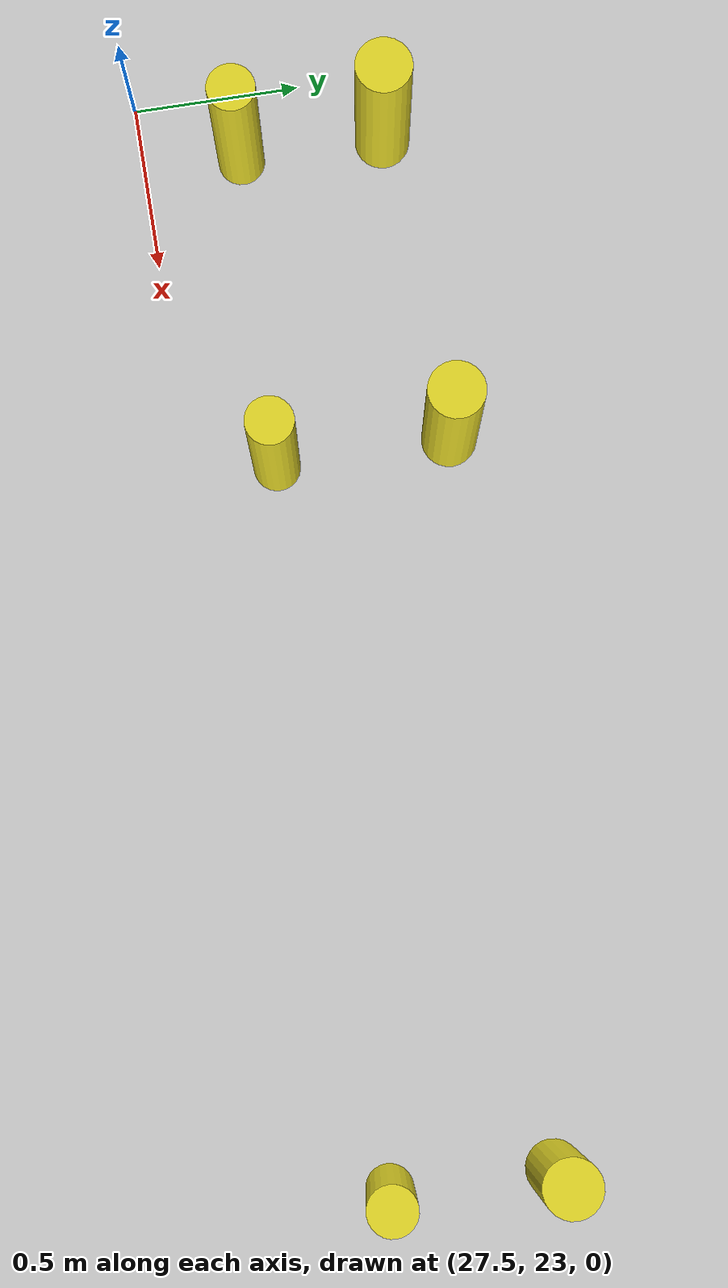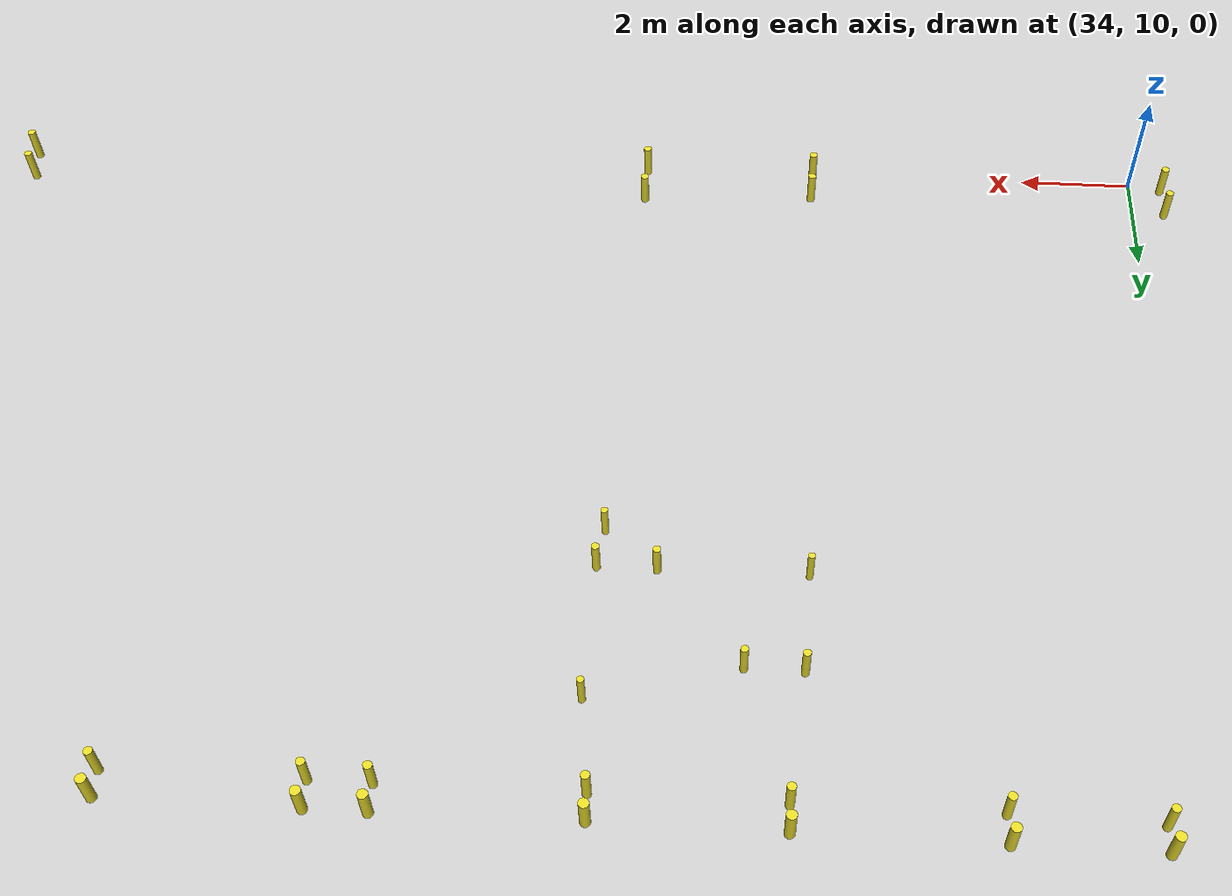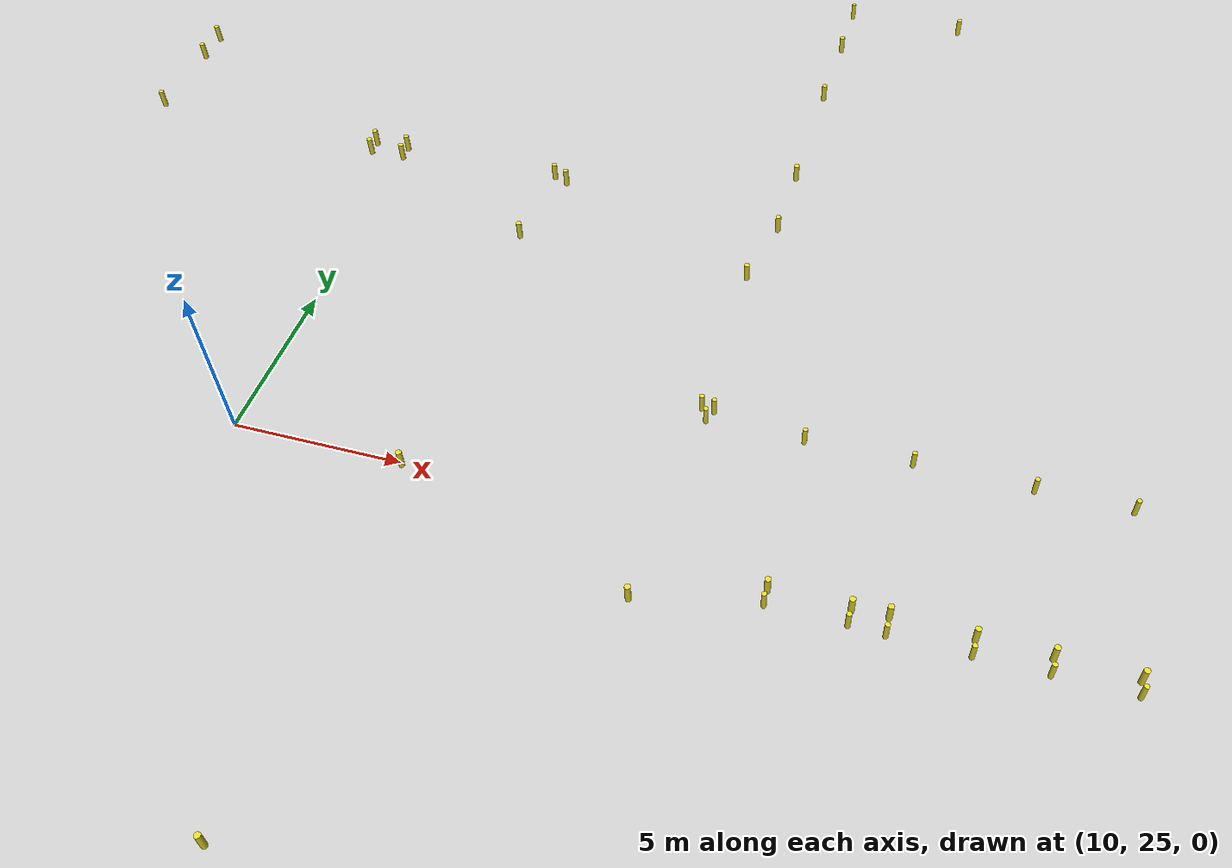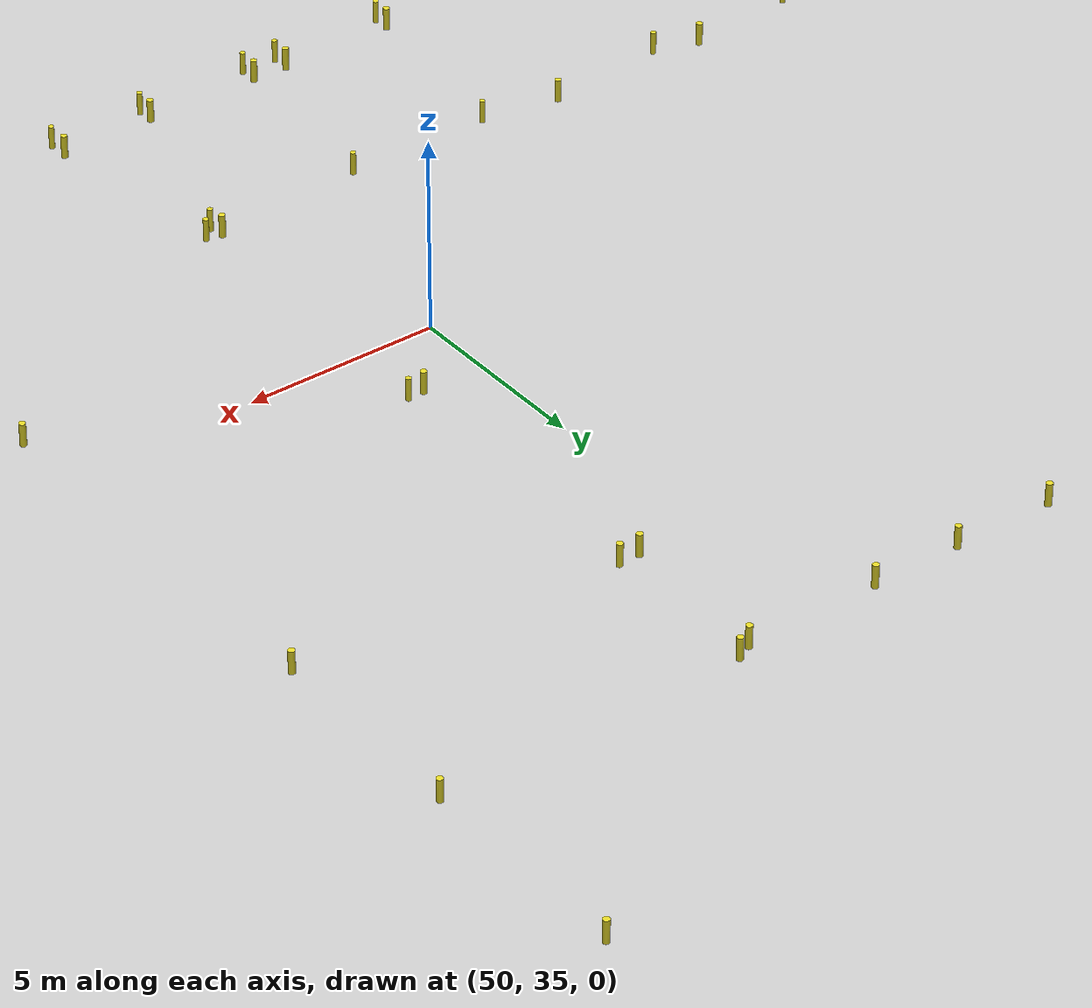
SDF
<sdf version="1.6">
 <world name="default">
  <light name="sun" type="directional">
   <pose>0 0 10 0 -0 0</pose>
   <diffuse>0.8 0.8 0.8 1</diffuse>
   <specular>0.1 0.1 0.1 1</specular>
   <attenuation>
    <range>1000</range>
    <constant>0.9</constant>
    <linear>0.01</linear>
    <quadratic>0.001</quadratic>
   </attenuation>
   <direction>-0.5 0.5 -1</direction>
  </light>
  <model name="ground_plane">
   <static>1</static>
   <link name="link">
    <collision name="collision">
     <geometry><plane><normal>0 0 1</normal><size>1000 1000</size></plane></geometry>
     <surface><friction><ode><mu>100</mu><mu2>50</mu2></ode></friction></surface>
    </collision>
    <visual name="visual">
     <cast_shadows>0</cast_shadows>
     <geometry><plane><normal>0 0 1</normal><size>1000 1000</size></plane></geometry>
     <material>
      <script><uri>file://media/materials/scripts/gazebo.material</uri><name>Gazebo/Grey</name></script>
     </material>
     <transparency>0.5</transparency>
    </visual>
   </link>
  </model>
  <gravity>0 0 -9.8</gravity>
  <magnetic_field>6e-06 2.3e-05 -4.2e-05</magnetic_field>
  <atmosphere type="adiabatic"/>
  <physics name="default_physics" default="1" type="ode">
   <max_step_size>0.02</max_step_size>
   <real_time_factor>1</real_time_factor>
   <real_time_update_rate>50</real_time_update_rate>
  </physics>
  <scene><ambient>0.4 0.4 0.4 1</ambient><background>0.7 0.7 0.7 1</background><shadows>1</shadows></scene>
  <spherical_coordinates>
   <surface_model>EARTH_WGS84</surface_model>
   <latitude_deg>0</latitude_deg>
   <longitude_deg>0</longitude_deg>
   <elevation>0</elevation>
   <heading_deg>0</heading_deg>
  </spherical_coordinates>
  <model name="bollards">
   <static>1</static>
   <link name="bollard_0">
    <pose>28.66787634671782 23.25938597836279 0 0 0 0</pose>
    <visual name="bollard_0_visual">
     <pose>0 0 0.3 0 0 0</pose>
     <geometry><cylinder><radius>0.07</radius><length>0.6</length></cylinder></geometry>
     <material>
      <script><uri>file://media/materials/scripts/gazebo.material</uri><name>Gazebo/Yellow</name></script>
     </material>
    </visual>
    <collision name="bollard_0_collision">
     <pose>0 0 0.3 0 0 0</pose>
     <geometry><cylinder><radius>0.07</radius><length>0.6</length></cylinder></geometry>
     <laser_retro>9000.0</laser_retro>
    </collision>
   </link>
   <link name="bollard_1">
    <pose>27.71043841671782 23.29701097836278 0 0 0 0</pose>
    <visual name="bollard_1_visual">
     <pose>0 0 0.3 0 0 0</pose>
     <geometry><cylinder><radius>0.07</radius><length>0.6</length></cylinder></geometry>
     <material>
      <script><uri>file://media/materials/scripts/gazebo.material</uri><name>Gazebo/Yellow</name></script>
     </material>
    </visual>
    <collision name="bollard_1_collision">
     <pose>0 0 0.3 0 0 0</pose>
     <geometry><cylinder><radius>0.07</radius><length>0.6</length></cylinder></geometry>
     <laser_retro>9000.0</laser_retro>
    </collision>
   </link>
   <link name="bollard_2">
    <pose>32.69640841671782 23.25701097836279 0 0 0 0</pose>
    <visual name="bollard_2_visual">
     <pose>0 0 0.3 0 0 0</pose>
     <geometry><cylinder><radius>0.07</radius><length>0.6</length></cylinder></geometry>
     <material>
      <script><uri>file://media/materials/scripts/gazebo.material</uri><name>Gazebo/Yellow</name></script>
     </material>
    </visual>
    <collision name="bollard_2_collision">
     <pose>0 0 0.3 0 0 0</pose>
     <geometry><cylinder><radius>0.07</radius><length>0.6</length></cylinder></geometry>
     <laser_retro>9000.0</laser_retro>
    </collision>
   </link>
   <link name="bollard_3">
    <pose>34.82375841671782 23.25701097836279 0 0 0 0</pose>
    <visual name="bollard_3_visual">
     <pose>0 0 0.3 0 0 0</pose>
     <geometry><cylinder><radius>0.07</radius><length>0.6</length></cylinder></geometry>
     <material>
      <script><uri>file://media/materials/scripts/gazebo.material</uri><name>Gazebo/Yellow</name></script>
     </material>
    </visual>
    <collision name="bollard_3_collision">
     <pose>0 0 0.3 0 0 0</pose>
     <geometry><cylinder><radius>0.07</radius><length>0.6</length></cylinder></geometry>
     <laser_retro>9000.0</laser_retro>
    </collision>
   </link>
   <link name="bollard_4">
    <pose>37.08335677571782 23.20802269736278 0 0 0 0</pose>
    <visual name="bollard_4_visual">
     <pose>0 0 0.3 0 0 0</pose>
     <geometry><cylinder><radius>0.07</radius><length>0.6</length></cylinder></geometry>
     <material>
      <script><uri>file://media/materials/scripts/gazebo.material</uri><name>Gazebo/Yellow</name></script>
     </material>
    </visual>
    <collision name="bollard_4_collision">
     <pose>0 0 0.3 0 0 0</pose>
     <geometry><cylinder><radius>0.07</radius><length>0.6</length></cylinder></geometry>
     <laser_retro>9000.0</laser_retro>
    </collision>
   </link>
   <link name="bollard_5">
    <pose>40.17118841671783 23.24701097836278 0 0 0 0</pose>
    <visual name="bollard_5_visual">
     <pose>0 0 0.3 0 0 0</pose>
     <geometry><cylinder><radius>0.07</radius><length>0.6</length></cylinder></geometry>
     <material>
      <script><uri>file://media/materials/scripts/gazebo.material</uri><name>Gazebo/Yellow</name></script>
     </material>
    </visual>
    <collision name="bollard_5_collision">
     <pose>0 0 0.3 0 0 0</pose>
     <geometry><cylinder><radius>0.07</radius><length>0.6</length></cylinder></geometry>
     <laser_retro>9000.0</laser_retro>
    </collision>
   </link>
   <link name="bollard_6">
    <pose>43.08078841671782 23.24701097836278 0 0 0 0</pose>
    <visual name="bollard_6_visual">
     <pose>0 0 0.3 0 0 0</pose>
     <geometry><cylinder><radius>0.07</radius><length>0.6</length></cylinder></geometry>
     <material>
      <script><uri>file://media/materials/scripts/gazebo.material</uri><name>Gazebo/Yellow</name></script>
     </material>
    </visual>
    <collision name="bollard_6_collision">
     <pose>0 0 0.3 0 0 0</pose>
     <geometry><cylinder><radius>0.07</radius><length>0.6</length></cylinder></geometry>
     <laser_retro>9000.0</laser_retro>
    </collision>
   </link>
   <link name="bollard_7">
    <pose>46.17078841671782 23.27701097836279 0 0 0 0</pose>
    <visual name="bollard_7_visual">
     <pose>0 0 0.3 0 0 0</pose>
     <geometry><cylinder><radius>0.07</radius><length>0.6</length></cylinder></geometry>
     <material>
      <script><uri>file://media/materials/scripts/gazebo.material</uri><name>Gazebo/Yellow</name></script>
     </material>
    </visual>
    <collision name="bollard_7_collision">
     <pose>0 0 0.3 0 0 0</pose>
     <geometry><cylinder><radius>0.07</radius><length>0.6</length></cylinder></geometry>
     <laser_retro>9000.0</laser_retro>
    </collision>
   </link>
   <link name="bollard_8">
    <pose>47.13078841671782 23.27701097836279 0 0 0 0</pose>
    <visual name="bollard_8_visual">
     <pose>0 0 0.3 0 0 0</pose>
     <geometry><cylinder><radius>0.07</radius><length>0.6</length></cylinder></geometry>
     <material>
      <script><uri>file://media/materials/scripts/gazebo.material</uri><name>Gazebo/Yellow</name></script>
     </material>
    </visual>
    <collision name="bollard_8_collision">
     <pose>0 0 0.3 0 0 0</pose>
     <geometry><cylinder><radius>0.07</radius><length>0.6</length></cylinder></geometry>
     <laser_retro>9000.0</laser_retro>
    </collision>
   </link>
   <link name="bollard_9">
    <pose>50.18078841671782 23.29701097836278 0 0 0 0</pose>
    <visual name="bollard_9_visual">
     <pose>0 0 0.3 0 0 0</pose>
     <geometry><cylinder><radius>0.07</radius><length>0.6</length></cylinder></geometry>
     <material>
      <script><uri>file://media/materials/scripts/gazebo.material</uri><name>Gazebo/Yellow</name></script>
     </material>
    </visual>
    <collision name="bollard_9_collision">
     <pose>0 0 0.3 0 0 0</pose>
     <geometry><cylinder><radius>0.07</radius><length>0.6</length></cylinder></geometry>
     <laser_retro>9000.0</laser_retro>
    </collision>
   </link>
   <link name="bollard_10">
    <pose>52.73078841671782 23.29701097836278 0 0 0 0</pose>
    <visual name="bollard_10_visual">
     <pose>0 0 0.3 0 0 0</pose>
     <geometry><cylinder><radius>0.07</radius><length>0.6</length></cylinder></geometry>
     <material>
      <script><uri>file://media/materials/scripts/gazebo.material</uri><name>Gazebo/Yellow</name></script>
     </material>
    </visual>
    <collision name="bollard_10_collision">
     <pose>0 0 0.3 0 0 0</pose>
     <geometry><cylinder><radius>0.07</radius><length>0.6</length></cylinder></geometry>
     <laser_retro>9000.0</laser_retro>
    </collision>
   </link>
   <link name="bollard_11">
    <pose>25.57431841671782 23.29701097836278 0 0 0 0</pose>
    <visual name="bollard_11_visual">
     <pose>0 0 0.3 0 0 0</pose>
     <geometry><cylinder><radius>0.07</radius><length>0.6</length></cylinder></geometry>
     <material>
      <script><uri>file://media/materials/scripts/gazebo.material</uri><name>Gazebo/Yellow</name></script>
     </material>
    </visual>
    <collision name="bollard_11_collision">
     <pose>0 0 0.3 0 0 0</pose>
     <geometry><cylinder><radius>0.07</radius><length>0.6</length></cylinder></geometry>
     <laser_retro>9000.0</laser_retro>
    </collision>
   </link>
   <link name="bollard_12">
    <pose>57.03724740071782 10.30733275536279 0 0 0 0</pose>
    <visual name="bollard_12_visual">
     <pose>0 0 0.3 0 0 0</pose>
     <geometry><cylinder><radius>0.07</radius><length>0.6</length></cylinder></geometry>
     <material>
      <script><uri>file://media/materials/scripts/gazebo.material</uri><name>Gazebo/Yellow</name></script>
     </material>
    </visual>
    <collision name="bollard_12_collision">
     <pose>0 0 0.3 0 0 0</pose>
     <geometry><cylinder><radius>0.07</radius><length>0.6</length></cylinder></geometry>
     <laser_retro>9000.0</laser_retro>
    </collision>
   </link>
   <link name="bollard_13">
    <pose>43.14779720571782 10.13399047036279 0 0 0 0</pose>
    <visual name="bollard_13_visual">
     <pose>0 0 0.3 0 0 0</pose>
     <geometry><cylinder><radius>0.07</radius><length>0.6</length></cylinder></geometry>
     <material>
      <script><uri>file://media/materials/scripts/gazebo.material</uri><name>Gazebo/Yellow</name></script>
     </material>
    </visual>
    <collision name="bollard_13_collision">
     <pose>0 0 0.3 0 0 0</pose>
     <geometry><cylinder><radius>0.07</radius><length>0.6</length></cylinder></geometry>
     <laser_retro>9000.0</laser_retro>
    </collision>
   </link>
   <link name="bollard_14">
    <pose>40.00598763571782 10.11794261936278 0 0 0 0</pose>
    <visual name="bollard_14_visual">
     <pose>0 0 0.3 0 0 0</pose>
     <geometry><cylinder><radius>0.07</radius><length>0.6</length></cylinder></geometry>
     <material>
      <script><uri>file://media/materials/scripts/gazebo.material</uri><name>Gazebo/Yellow</name></script>
     </material>
    </visual>
    <collision name="bollard_14_collision">
     <pose>0 0 0.3 0 0 0</pose>
     <geometry><cylinder><radius>0.07</radius><length>0.6</length></cylinder></geometry>
     <laser_retro>9000.0</laser_retro>
    </collision>
   </link>
   <link name="bollard_15">
    <pose>33.42140252171782 10.12617259936278 0 0 0 0</pose>
    <visual name="bollard_15_visual">
     <pose>0 0 0.3 0 0 0</pose>
     <geometry><cylinder><radius>0.07</radius><length>0.6</length></cylinder></geometry>
     <material>
      <script><uri>file://media/materials/scripts/gazebo.material</uri><name>Gazebo/Yellow</name></script>
     </material>
    </visual>
    <collision name="bollard_15_collision">
     <pose>0 0 0.3 0 0 0</pose>
     <geometry><cylinder><radius>0.07</radius><length>0.6</length></cylinder></geometry>
     <laser_retro>9000.0</laser_retro>
    </collision>
   </link>
   <link name="bollard_16">
    <pose>54.94420638571781 10.37870580236279 0 0 0 0</pose>
    <visual name="bollard_16_visual">
     <pose>0 0 0.3 0 0 0</pose>
     <geometry><cylinder><radius>0.07</radius><length>0.6</length></cylinder></geometry>
     <material>
      <script><uri>file://media/materials/scripts/gazebo.material</uri><name>Gazebo/Yellow</name></script>
     </material>
    </visual>
    <collision name="bollard_16_collision">
     <pose>0 0 0.3 0 0 0</pose>
     <geometry><cylinder><radius>0.07</radius><length>0.6</length></cylinder></geometry>
     <laser_retro>9000.0</laser_retro>
    </collision>
   </link>
   <link name="bollard_17">
    <pose>30.79575841671782 23.25701097836279 0 0 0 0</pose>
    <visual name="bollard_17_visual">
     <pose>0 0 0.3 0 0 0</pose>
     <geometry><cylinder><radius>0.07</radius><length>0.6</length></cylinder></geometry>
     <material>
      <script><uri>file://media/materials/scripts/gazebo.material</uri><name>Gazebo/Yellow</name></script>
     </material>
    </visual>
    <collision name="bollard_17_collision">
     <pose>0 0 0.3 0 0 0</pose>
     <geometry><cylinder><radius>0.07</radius><length>0.6</length></cylinder></geometry>
     <laser_retro>9000.0</laser_retro>
    </collision>
   </link>
   <link name="bollard_18">
    <pose>39.98065841671782 21.05477308736279 0 0 0 0</pose>
    <visual name="bollard_18_visual">
     <pose>0 0 0.3 0 0 0</pose>
     <geometry><cylinder><radius>0.0635</radius><length>0.6</length></cylinder></geometry>
     <material>
      <script><uri>file://media/materials/scripts/gazebo.material</uri><name>Gazebo/Yellow</name></script>
     </material>
    </visual>
    <collision name="bollard_18_collision">
     <pose>0 0 0.3 0 0 0</pose>
     <geometry><cylinder><radius>0.0635</radius><length>0.6</length></cylinder></geometry>
     <laser_retro>9000.0</laser_retro>
    </collision>
   </link>
   <link name="bollard_19">
    <pose>39.93698410071782 19.30418187636279 0 0 0 0</pose>
    <visual name="bollard_19_visual">
     <pose>0 0 0.3 0 0 0</pose>
     <geometry><cylinder><radius>0.055</radius><length>0.6</length></cylinder></geometry>
     <material>
      <script><uri>file://media/materials/scripts/gazebo.material</uri><name>Gazebo/Yellow</name></script>
     </material>
    </visual>
    <collision name="bollard_19_collision">
     <pose>0 0 0.3 0 0 0</pose>
     <geometry><cylinder><radius>0.055</radius><length>0.6</length></cylinder></geometry>
     <laser_retro>9000.0</laser_retro>
    </collision>
   </link>
   <link name="bollard_20">
    <pose>43.15078841671782 10.89974097836278 0 0 0 0</pose>
    <visual name="bollard_20_visual">
     <pose>0 0 0.3 0 0 0</pose>
     <geometry><cylinder><radius>0.07</radius><length>0.6</length></cylinder></geometry>
     <material>
      <script><uri>file://media/materials/scripts/gazebo.material</uri><name>Gazebo/Yellow</name></script>
     </material>
    </visual>
    <collision name="bollard_20_collision">
     <pose>0 0 0.3 0 0 0</pose>
     <geometry><cylinder><radius>0.07</radius><length>0.6</length></cylinder></geometry>
     <laser_retro>9000.0</laser_retro>
    </collision>
   </link>
   <link name="bollard_21">
    <pose>54.83078841671782 10.97201097836279 0 0 0 0</pose>
    <visual name="bollard_21_visual">
     <pose>0 0 0.3 0 0 0</pose>
     <geometry><cylinder><radius>0.07</radius><length>0.6</length></cylinder></geometry>
     <material>
      <script><uri>file://media/materials/scripts/gazebo.material</uri><name>Gazebo/Yellow</name></script>
     </material>
    </visual>
    <collision name="bollard_21_collision">
     <pose>0 0 0.3 0 0 0</pose>
     <geometry><cylinder><radius>0.07</radius><length>0.6</length></cylinder></geometry>
     <laser_retro>9000.0</laser_retro>
    </collision>
   </link>
   <link name="bollard_22">
    <pose>33.41653316771782 10.76738890836278 0 0 0 0</pose>
    <visual name="bollard_22_visual">
     <pose>0 0 0.3 0 0 0</pose>
     <geometry><cylinder><radius>0.07</radius><length>0.6</length></cylinder></geometry>
     <material>
      <script><uri>file://media/materials/scripts/gazebo.material</uri><name>Gazebo/Yellow</name></script>
     </material>
    </visual>
    <collision name="bollard_22_collision">
     <pose>0 0 0.3 0 0 0</pose>
     <geometry><cylinder><radius>0.07</radius><length>0.6</length></cylinder></geometry>
     <laser_retro>9000.0</laser_retro>
    </collision>
   </link>
   <link name="bollard_23">
    <pose>40.02698031171782 10.70332347836279 0 0 0 0</pose>
    <visual name="bollard_23_visual">
     <pose>0 0 0.3 0 0 0</pose>
     <geometry><cylinder><radius>0.07</radius><length>0.6</length></cylinder></geometry>
     <material>
      <script><uri>file://media/materials/scripts/gazebo.material</uri><name>Gazebo/Yellow</name></script>
     </material>
    </visual>
    <collision name="bollard_23_collision">
     <pose>0 0 0.3 0 0 0</pose>
     <geometry><cylinder><radius>0.07</radius><length>0.6</length></cylinder></geometry>
     <laser_retro>9000.0</laser_retro>
    </collision>
   </link>
   <link name="bollard_24">
    <pose>43.22074544771782 18.62802032636278 0 0 0 0</pose>
    <visual name="bollard_24_visual">
     <pose>0 0 0.3 0 0 0</pose>
     <geometry><cylinder><radius>0.0575</radius><length>0.6</length></cylinder></geometry>
     <material>
      <script><uri>file://media/materials/scripts/gazebo.material</uri><name>Gazebo/Yellow</name></script>
     </material>
    </visual>
    <collision name="bollard_24_collision">
     <pose>0 0 0.3 0 0 0</pose>
     <geometry><cylinder><radius>0.0575</radius><length>0.6</length></cylinder></geometry>
     <laser_retro>9000.0</laser_retro>
    </collision>
   </link>
   <link name="bollard_25">
    <pose>43.30127841671782 19.32901097836278 0 0 0 0</pose>
    <visual name="bollard_25_visual">
     <pose>0 0 0.3 0 0 0</pose>
     <geometry><cylinder><radius>0.0635</radius><length>0.6</length></cylinder></geometry>
     <material>
      <script><uri>file://media/materials/scripts/gazebo.material</uri><name>Gazebo/Yellow</name></script>
     </material>
    </visual>
    <collision name="bollard_25_collision">
     <pose>0 0 0.3 0 0 0</pose>
     <geometry><cylinder><radius>0.0635</radius><length>0.6</length></cylinder></geometry>
     <laser_retro>9000.0</laser_retro>
    </collision>
   </link>
   <link name="bollard_26">
    <pose>42.34127841671782 19.32901097836278 0 0 0 0</pose>
    <visual name="bollard_26_visual">
     <pose>0 0 0.3 0 0 0</pose>
     <geometry><cylinder><radius>0.0635</radius><length>0.6</length></cylinder></geometry>
     <material>
      <script><uri>file://media/materials/scripts/gazebo.material</uri><name>Gazebo/Yellow</name></script>
     </material>
    </visual>
    <collision name="bollard_26_collision">
     <pose>0 0 0.3 0 0 0</pose>
     <geometry><cylinder><radius>0.0635</radius><length>0.6</length></cylinder></geometry>
     <laser_retro>9000.0</laser_retro>
    </collision>
   </link>
   <link name="bollard_27">
    <pose>40.91203353371782 21.04397679836278 0 0 0 0</pose>
    <visual name="bollard_27_visual">
     <pose>0 0 0.3 0 0 0</pose>
     <geometry><cylinder><radius>0.061778606</radius><length>0.6</length></cylinder></geometry>
     <material>
      <script><uri>file://media/materials/scripts/gazebo.material</uri><name>Gazebo/Yellow</name></script>
     </material>
    </visual>
    <collision name="bollard_27_collision">
     <pose>0 0 0.3 0 0 0</pose>
     <geometry><cylinder><radius>0.061778606</radius><length>0.6</length></cylinder></geometry>
     <laser_retro>9000.0</laser_retro>
    </collision>
   </link>
   <link name="bollard_28">
    <pose>43.30127841671782 21.71101097836279 0 0 0 0</pose>
    <visual name="bollard_28_visual">
     <pose>0 0 0.3 0 0 0</pose>
     <geometry><cylinder><radius>0.0575</radius><length>0.6</length></cylinder></geometry>
     <material>
      <script><uri>file://media/materials/scripts/gazebo.material</uri><name>Gazebo/Yellow</name></script>
     </material>
    </visual>
    <collision name="bollard_28_collision">
     <pose>0 0 0.3 0 0 0</pose>
     <geometry><cylinder><radius>0.0575</radius><length>0.6</length></cylinder></geometry>
     <laser_retro>9000.0</laser_retro>
    </collision>
   </link>
   <link name="bollard_29">
    <pose>25.53363851471782 9.98040111536278 0 0 0 0</pose>
    <visual name="bollard_29_visual">
     <pose>0 0 0.3 0 0 0</pose>
     <geometry><cylinder><radius>0.0825</radius><length>0.6</length></cylinder></geometry>
     <material>
      <script><uri>file://media/materials/scripts/gazebo.material</uri><name>Gazebo/Yellow</name></script>
     </material>
    </visual>
    <collision name="bollard_29_collision">
     <pose>0 0 0.3 0 0 0</pose>
     <geometry><cylinder><radius>0.0825</radius><length>0.6</length></cylinder></geometry>
     <laser_retro>9000.0</laser_retro>
    </collision>
   </link>
   <link name="bollard_30">
    <pose>31.53363851471782 9.95544554836279 0 0 0 0</pose>
    <visual name="bollard_30_visual">
     <pose>0 0 0.3 0 0 0</pose>
     <geometry><cylinder><radius>0.0825</radius><length>0.6</length></cylinder></geometry>
     <material>
      <script><uri>file://media/materials/scripts/gazebo.material</uri><name>Gazebo/Yellow</name></script>
     </material>
    </visual>
    <collision name="bollard_30_collision">
     <pose>0 0 0.3 0 0 0</pose>
     <geometry><cylinder><radius>0.0825</radius><length>0.6</length></cylinder></geometry>
     <laser_retro>9000.0</laser_retro>
    </collision>
   </link>
   <link name="bollard_31">
    <pose>31.52140316271782 10.71170983736279 0 0 0 0</pose>
    <visual name="bollard_31_visual">
     <pose>0 0 0.3 0 0 0</pose>
     <geometry><cylinder><radius>0.07</radius><length>0.6</length></cylinder></geometry>
     <material>
      <script><uri>file://media/materials/scripts/gazebo.material</uri><name>Gazebo/Yellow</name></script>
     </material>
    </visual>
    <collision name="bollard_31_collision">
     <pose>0 0 0.3 0 0 0</pose>
     <geometry><cylinder><radius>0.07</radius><length>0.6</length></cylinder></geometry>
     <laser_retro>9000.0</laser_retro>
    </collision>
   </link>
   <link name="bollard_32">
    <pose>25.52619613171782 10.75780736536279 0 0 0 0</pose>
    <visual name="bollard_32_visual">
     <pose>0 0 0.3 0 0 0</pose>
     <geometry><cylinder><radius>0.07</radius><length>0.6</length></cylinder></geometry>
     <material>
      <script><uri>file://media/materials/scripts/gazebo.material</uri><name>Gazebo/Yellow</name></script>
     </material>
    </visual>
    <collision name="bollard_32_collision">
     <pose>0 0 0.3 0 0 0</pose>
     <geometry><cylinder><radius>0.07</radius><length>0.6</length></cylinder></geometry>
     <laser_retro>9000.0</laser_retro>
    </collision>
   </link>
   <link name="bollard_33">
    <pose>22.86077999732971 48.65999245817022 0 0 0 0</pose>
    <visual name="bollard_33_visual">
     <pose>0 0 0.3 0 0 0</pose>
     <geometry><cylinder><radius>0.07</radius><length>0.6</length></cylinder></geometry>
     <material>
      <script><uri>file://media/materials/scripts/gazebo.material</uri><name>Gazebo/Yellow</name></script>
     </material>
    </visual>
    <collision name="bollard_33_collision">
     <pose>0 0 0.3 0 0 0</pose>
     <geometry><cylinder><radius>0.07</radius><length>0.6</length></cylinder></geometry>
     <laser_retro>9000.0</laser_retro>
    </collision>
   </link>
   <link name="bollard_34">
    <pose>22.77720393195824 28.9591303548362 0 0 0 0</pose>
    <visual name="bollard_34_visual">
     <pose>0 0 0.3 0 0 0</pose>
     <geometry><cylinder><radius>0.07</radius><length>0.6</length></cylinder></geometry>
     <material>
      <script><uri>file://media/materials/scripts/gazebo.material</uri><name>Gazebo/Yellow</name></script>
     </material>
    </visual>
    <collision name="bollard_34_collision">
     <pose>0 0 0.3 0 0 0</pose>
     <geometry><cylinder><radius>0.07</radius><length>0.6</length></cylinder></geometry>
     <laser_retro>9000.0</laser_retro>
    </collision>
   </link>
   <link name="bollard_35">
    <pose>22.85489695615665 46.51771325623102 0 0 0 0</pose>
    <visual name="bollard_35_visual">
     <pose>0 0 0.3 0 0 0</pose>
     <geometry><cylinder><radius>0.0825</radius><length>0.6</length></cylinder></geometry>
     <material>
      <script><uri>file://media/materials/scripts/gazebo.material</uri><name>Gazebo/Yellow</name></script>
     </material>
    </visual>
    <collision name="bollard_35_collision">
     <pose>0 0 0.3 0 0 0</pose>
     <geometry><cylinder><radius>0.0825</radius><length>0.6</length></cylinder></geometry>
     <laser_retro>9000.0</laser_retro>
    </collision>
   </link>
   <link name="bollard_36">
    <pose>22.81119224601908 43.59896800261672 0 0 0 0</pose>
    <visual name="bollard_36_visual">
     <pose>0 0 0.3 0 0 0</pose>
     <geometry><cylinder><radius>0.0825</radius><length>0.6</length></cylinder></geometry>
     <material>
      <script><uri>file://media/materials/scripts/gazebo.material</uri><name>Gazebo/Yellow</name></script>
     </material>
    </visual>
    <collision name="bollard_36_collision">
     <pose>0 0 0.3 0 0 0</pose>
     <geometry><cylinder><radius>0.0825</radius><length>0.6</length></cylinder></geometry>
     <laser_retro>9000.0</laser_retro>
    </collision>
   </link>
   <link name="bollard_37">
    <pose>22.80976627751159 39.21238690381055 0 0 0 0</pose>
    <visual name="bollard_37_visual">
     <pose>0 0 0.3 0 0 0</pose>
     <geometry><cylinder><radius>0.0825</radius><length>0.6</length></cylinder></geometry>
     <material>
      <script><uri>file://media/materials/scripts/gazebo.material</uri><name>Gazebo/Yellow</name></script>
     </material>
    </visual>
    <collision name="bollard_37_collision">
     <pose>0 0 0.3 0 0 0</pose>
     <geometry><cylinder><radius>0.0825</radius><length>0.6</length></cylinder></geometry>
     <laser_retro>9000.0</laser_retro>
    </collision>
   </link>
   <link name="bollard_38">
    <pose>22.79241169121367 36.66709578730043 0 0 0 0</pose>
    <visual name="bollard_38_visual">
     <pose>0 0 0.3 0 0 0</pose>
     <geometry><cylinder><radius>0.0825</radius><length>0.6</length></cylinder></geometry>
     <material>
      <script><uri>file://media/materials/scripts/gazebo.material</uri><name>Gazebo/Yellow</name></script>
     </material>
    </visual>
    <collision name="bollard_38_collision">
     <pose>0 0 0.3 0 0 0</pose>
     <geometry><cylinder><radius>0.0825</radius><length>0.6</length></cylinder></geometry>
     <laser_retro>9000.0</laser_retro>
    </collision>
   </link>
   <link name="bollard_39">
    <pose>51.65679969368406 28.98252161204334 0 0 0 0</pose>
    <visual name="bollard_39_visual">
     <pose>0 0 0.3 0 0 0</pose>
     <geometry><cylinder><radius>0.0825</radius><length>0.6</length></cylinder></geometry>
     <material>
      <script><uri>file://media/materials/scripts/gazebo.material</uri><name>Gazebo/Yellow</name></script>
     </material>
    </visual>
    <collision name="bollard_39_collision">
     <pose>0 0 0.3 0 0 0</pose>
     <geometry><cylinder><radius>0.0825</radius><length>0.6</length></cylinder></geometry>
     <laser_retro>9000.0</laser_retro>
    </collision>
   </link>
   <link name="bollard_40">
    <pose>51.57934369236649 44.7471250157462 0 0 0 0</pose>
    <visual name="bollard_40_visual">
     <pose>0 0 0.3 0 0 0</pose>
     <geometry><cylinder><radius>0.0825</radius><length>0.6</length></cylinder></geometry>
     <material>
      <script><uri>file://media/materials/scripts/gazebo.material</uri><name>Gazebo/Yellow</name></script>
     </material>
    </visual>
    <collision name="bollard_40_collision">
     <pose>0 0 0.3 0 0 0</pose>
     <geometry><cylinder><radius>0.0825</radius><length>0.6</length></cylinder></geometry>
     <laser_retro>9000.0</laser_retro>
    </collision>
   </link>
   <link name="bollard_41">
    <pose>52.13255126010264 44.76704663460067 0 0 0 0</pose>
    <visual name="bollard_41_visual">
     <pose>0 0 0.3 0 0 0</pose>
     <geometry><cylinder><radius>0.0825</radius><length>0.6</length></cylinder></geometry>
     <material>
      <script><uri>file://media/materials/scripts/gazebo.material</uri><name>Gazebo/Yellow</name></script>
     </material>
    </visual>
    <collision name="bollard_41_collision">
     <pose>0 0 0.3 0 0 0</pose>
     <geometry><cylinder><radius>0.0825</radius><length>0.6</length></cylinder></geometry>
     <laser_retro>9000.0</laser_retro>
    </collision>
   </link>
   <link name="bollard_42">
    <pose>52.13988063518823 48.88522518469232 0 0 0 0</pose>
    <visual name="bollard_42_visual">
     <pose>0 0 0.3 0 0 0</pose>
     <geometry><cylinder><radius>0.0825</radius><length>0.6</length></cylinder></geometry>
     <material>
      <script><uri>file://media/materials/scripts/gazebo.material</uri><name>Gazebo/Yellow</name></script>
     </material>
    </visual>
    <collision name="bollard_42_collision">
     <pose>0 0 0.3 0 0 0</pose>
     <geometry><cylinder><radius>0.0825</radius><length>0.6</length></cylinder></geometry>
     <laser_retro>9000.0</laser_retro>
    </collision>
   </link>
   <link name="bollard_43">
    <pose>51.73501561196213 48.68279267307927 0 0 0 0</pose>
    <visual name="bollard_43_visual">
     <pose>0 0 0.3 0 0 0</pose>
     <geometry><cylinder><radius>0.0825</radius><length>0.6</length></cylinder></geometry>
     <material>
      <script><uri>file://media/materials/scripts/gazebo.material</uri><name>Gazebo/Yellow</name></script>
     </material>
    </visual>
    <collision name="bollard_43_collision">
     <pose>0 0 0.3 0 0 0</pose>
     <geometry><cylinder><radius>0.0825</radius><length>0.6</length></cylinder></geometry>
     <laser_retro>9000.0</laser_retro>
    </collision>
   </link>
   <link name="bollard_44">
    <pose>48.24121575788488 48.66510892210199 0 0 0 0</pose>
    <visual name="bollard_44_visual">
     <pose>0 0 0.3 0 0 0</pose>
     <geometry><cylinder><radius>0.0825</radius><length>0.6</length></cylinder></geometry>
     <material>
      <script><uri>file://media/materials/scripts/gazebo.material</uri><name>Gazebo/Yellow</name></script>
     </material>
    </visual>
    <collision name="bollard_44_collision">
     <pose>0 0 0.3 0 0 0</pose>
     <geometry><cylinder><radius>0.0825</radius><length>0.6</length></cylinder></geometry>
     <laser_retro>9000.0</laser_retro>
    </collision>
   </link>
   <link name="bollard_45">
    <pose>45.91184461923132 48.66510892210199 0 0 0 0</pose>
    <visual name="bollard_45_visual">
     <pose>0 0 0.3 0 0 0</pose>
     <geometry><cylinder><radius>0.0825</radius><length>0.6</length></cylinder></geometry>
     <material>
      <script><uri>file://media/materials/scripts/gazebo.material</uri><name>Gazebo/Yellow</name></script>
     </material>
    </visual>
    <collision name="bollard_45_collision">
     <pose>0 0 0.3 0 0 0</pose>
     <geometry><cylinder><radius>0.0825</radius><length>0.6</length></cylinder></geometry>
     <laser_retro>9000.0</laser_retro>
    </collision>
   </link>
   <link name="bollard_46">
    <pose>43.3048000998111 48.68053522103347 0 0 0 0</pose>
    <visual name="bollard_46_visual">
     <pose>0 0 0.3 0 0 0</pose>
     <geometry><cylinder><radius>0.0825</radius><length>0.6</length></cylinder></geometry>
     <material>
      <script><uri>file://media/materials/scripts/gazebo.material</uri><name>Gazebo/Yellow</name></script>
     </material>
    </visual>
    <collision name="bollard_46_collision">
     <pose>0 0 0.3 0 0 0</pose>
     <geometry><cylinder><radius>0.0825</radius><length>0.6</length></cylinder></geometry>
     <laser_retro>9000.0</laser_retro>
    </collision>
   </link>
   <link name="bollard_47">
    <pose>40.65147668359644 48.69596151996496 0 0 0 0</pose>
    <visual name="bollard_47_visual">
     <pose>0 0 0.3 0 0 0</pose>
     <geometry><cylinder><radius>0.0825</radius><length>0.6</length></cylinder></geometry>
     <material>
      <script><uri>file://media/materials/scripts/gazebo.material</uri><name>Gazebo/Yellow</name></script>
     </material>
    </visual>
    <collision name="bollard_47_collision">
     <pose>0 0 0.3 0 0 0</pose>
     <geometry><cylinder><radius>0.0825</radius><length>0.6</length></cylinder></geometry>
     <laser_retro>9000.0</laser_retro>
    </collision>
   </link>
   <link name="bollard_48">
    <pose>36.76423446845053 48.68004157946766 0 0 0 0</pose>
    <visual name="bollard_48_visual">
     <pose>0 0 0.3 0 0 0</pose>
     <geometry><cylinder><radius>0.0825</radius><length>0.6</length></cylinder></geometry>
     <material>
      <script><uri>file://media/materials/scripts/gazebo.material</uri><name>Gazebo/Yellow</name></script>
     </material>
    </visual>
    <collision name="bollard_48_collision">
     <pose>0 0 0.3 0 0 0</pose>
     <geometry><cylinder><radius>0.0825</radius><length>0.6</length></cylinder></geometry>
     <laser_retro>9000.0</laser_retro>
    </collision>
   </link>
   <link name="bollard_49">
    <pose>26.77733492748403 48.69850377402886 0 0 0 0</pose>
    <visual name="bollard_49_visual">
     <pose>0 0 0.3 0 0 0</pose>
     <geometry><cylinder><radius>0.0825</radius><length>0.6</length></cylinder></geometry>
     <material>
      <script><uri>file://media/materials/scripts/gazebo.material</uri><name>Gazebo/Yellow</name></script>
     </material>
    </visual>
    <collision name="bollard_49_collision">
     <pose>0 0 0.3 0 0 0</pose>
     <geometry><cylinder><radius>0.0825</radius><length>0.6</length></cylinder></geometry>
     <laser_retro>9000.0</laser_retro>
    </collision>
   </link>
   <link name="bollard_50">
    <pose>51.67053573725977 37.00024943638715 0 0 0 0</pose>
    <visual name="bollard_50_visual">
     <pose>0 0 0.3 0 0 0</pose>
     <geometry><cylinder><radius>0.0825</radius><length>0.6</length></cylinder></geometry>
     <material>
      <script><uri>file://media/materials/scripts/gazebo.material</uri><name>Gazebo/Yellow</name></script>
     </material>
    </visual>
    <collision name="bollard_50_collision">
     <pose>0 0 0.3 0 0 0</pose>
     <geometry><cylinder><radius>0.0825</radius><length>0.6</length></cylinder></geometry>
     <laser_retro>9000.0</laser_retro>
    </collision>
   </link>
   <link name="bollard_51">
    <pose>37.29894893700356 28.94194333852093 0 0 0 0</pose>
    <visual name="bollard_51_visual">
     <pose>0 0 0.3 0 0 0</pose>
     <geometry><cylinder><radius>0.0825</radius><length>0.6</length></cylinder></geometry>
     <material>
      <script><uri>file://media/materials/scripts/gazebo.material</uri><name>Gazebo/Yellow</name></script>
     </material>
    </visual>
    <collision name="bollard_51_collision">
     <pose>0 0 0.3 0 0 0</pose>
     <geometry><cylinder><radius>0.0825</radius><length>0.6</length></cylinder></geometry>
     <laser_retro>9000.0</laser_retro>
    </collision>
   </link>
   <link name="bollard_52">
    <pose>41.70629800305205 28.94194333852093 0 0 0 0</pose>
    <visual name="bollard_52_visual">
     <pose>0 0 0.3 0 0 0</pose>
     <geometry><cylinder><radius>0.0825</radius><length>0.6</length></cylinder></geometry>
     <material>
      <script><uri>file://media/materials/scripts/gazebo.material</uri><name>Gazebo/Yellow</name></script>
     </material>
    </visual>
    <collision name="bollard_52_collision">
     <pose>0 0 0.3 0 0 0</pose>
     <geometry><cylinder><radius>0.0825</radius><length>0.6</length></cylinder></geometry>
     <laser_retro>9000.0</laser_retro>
    </collision>
   </link>
   <link name="bollard_53">
    <pose>22.63143265345672 28.58923352322861 0 0 0 0</pose>
    <visual name="bollard_53_visual">
     <pose>0 0 0.3 0 0 0</pose>
     <geometry><cylinder><radius>0.07</radius><length>0.6</length></cylinder></geometry>
     <material>
      <script><uri>file://media/materials/scripts/gazebo.material</uri><name>Gazebo/Yellow</name></script>
     </material>
    </visual>
    <collision name="bollard_53_collision">
     <pose>0 0 0.3 0 0 0</pose>
     <geometry><cylinder><radius>0.07</radius><length>0.6</length></cylinder></geometry>
     <laser_retro>9000.0</laser_retro>
    </collision>
   </link>
   <link name="bollard_54">
    <pose>22.40244852869255 28.99899458859607 0 0 0 0</pose>
    <visual name="bollard_54_visual">
     <pose>0 0 0.3 0 0 0</pose>
     <geometry><cylinder><radius>0.07</radius><length>0.6</length></cylinder></geometry>
     <material>
      <script><uri>file://media/materials/scripts/gazebo.material</uri><name>Gazebo/Yellow</name></script>
     </material>
    </visual>
    <collision name="bollard_54_collision">
     <pose>0 0 0.3 0 0 0</pose>
     <geometry><cylinder><radius>0.07</radius><length>0.6</length></cylinder></geometry>
     <laser_retro>9000.0</laser_retro>
    </collision>
   </link>
   <link name="bollard_55">
    <pose>25.43950113082779 28.59525942124872 0 0 0 0</pose>
    <visual name="bollard_55_visual">
     <pose>0 0 0.3 0 0 0</pose>
     <geometry><cylinder><radius>0.07</radius><length>0.6</length></cylinder></geometry>
     <material>
      <script><uri>file://media/materials/scripts/gazebo.material</uri><name>Gazebo/Yellow</name></script>
     </material>
    </visual>
    <collision name="bollard_55_collision">
     <pose>0 0 0.3 0 0 0</pose>
     <geometry><cylinder><radius>0.07</radius><length>0.6</length></cylinder></geometry>
     <laser_retro>9000.0</laser_retro>
    </collision>
   </link>
   <link name="bollard_56">
    <pose>28.45702982337787 28.61005902678611 0 0 0 0</pose>
    <visual name="bollard_56_visual">
     <pose>0 0 0.3 0 0 0</pose>
     <geometry><cylinder><radius>0.07</radius><length>0.6</length></cylinder></geometry>
     <material>
      <script><uri>file://media/materials/scripts/gazebo.material</uri><name>Gazebo/Yellow</name></script>
     </material>
    </visual>
    <collision name="bollard_56_collision">
     <pose>0 0 0.3 0 0 0</pose>
     <geometry><cylinder><radius>0.07</radius><length>0.6</length></cylinder></geometry>
     <laser_retro>9000.0</laser_retro>
    </collision>
   </link>
   <link name="bollard_57">
    <pose>31.72991040369462 28.60906451257689 0 0 0 0</pose>
    <visual name="bollard_57_visual">
     <pose>0 0 0.3 0 0 0</pose>
     <geometry><cylinder><radius>0.07</radius><length>0.6</length></cylinder></geometry>
     <material>
      <script><uri>file://media/materials/scripts/gazebo.material</uri><name>Gazebo/Yellow</name></script>
     </material>
    </visual>
    <collision name="bollard_57_collision">
     <pose>0 0 0.3 0 0 0</pose>
     <geometry><cylinder><radius>0.07</radius><length>0.6</length></cylinder></geometry>
     <laser_retro>9000.0</laser_retro>
    </collision>
   </link>
   <link name="bollard_58">
    <pose>34.35885906241793 28.61710908643374 0 0 0 0</pose>
    <visual name="bollard_58_visual">
     <pose>0 0 0.3 0 0 0</pose>
     <geometry><cylinder><radius>0.07</radius><length>0.6</length></cylinder></geometry>
     <material>
      <script><uri>file://media/materials/scripts/gazebo.material</uri><name>Gazebo/Yellow</name></script>
     </material>
    </visual>
    <collision name="bollard_58_collision">
     <pose>0 0 0.3 0 0 0</pose>
     <geometry><cylinder><radius>0.07</radius><length>0.6</length></cylinder></geometry>
     <laser_retro>9000.0</laser_retro>
    </collision>
   </link>
   <link name="bollard_59">
    <pose>38.47517892426528 28.59637999724456 0 0 0 0</pose>
    <visual name="bollard_59_visual">
     <pose>0 0 0.3 0 0 0</pose>
     <geometry><cylinder><radius>0.07</radius><length>0.6</length></cylinder></geometry>
     <material>
      <script><uri>file://media/materials/scripts/gazebo.material</uri><name>Gazebo/Yellow</name></script>
     </material>
    </visual>
    <collision name="bollard_59_collision">
     <pose>0 0 0.3 0 0 0</pose>
     <geometry><cylinder><radius>0.07</radius><length>0.6</length></cylinder></geometry>
     <laser_retro>9000.0</laser_retro>
    </collision>
   </link>
   <link name="bollard_60">
    <pose>43.75756790162485 28.60680239046014 0 0 0 0</pose>
    <visual name="bollard_60_visual">
     <pose>0 0 0.3 0 0 0</pose>
     <geometry><cylinder><radius>0.07</radius><length>0.6</length></cylinder></geometry>
     <material>
      <script><uri>file://media/materials/scripts/gazebo.material</uri><name>Gazebo/Yellow</name></script>
     </material>
    </visual>
    <collision name="bollard_60_collision">
     <pose>0 0 0.3 0 0 0</pose>
     <geometry><cylinder><radius>0.07</radius><length>0.6</length></cylinder></geometry>
     <laser_retro>9000.0</laser_retro>
    </collision>
   </link>
   <link name="bollard_61">
    <pose>47.61503735983302 28.61542569156286 0 0 0 0</pose>
    <visual name="bollard_61_visual">
     <pose>0 0 0.3 0 0 0</pose>
     <geometry><cylinder><radius>0.07</radius><length>0.6</length></cylinder></geometry>
     <material>
      <script><uri>file://media/materials/scripts/gazebo.material</uri><name>Gazebo/Yellow</name></script>
     </material>
    </visual>
    <collision name="bollard_61_collision">
     <pose>0 0 0.3 0 0 0</pose>
     <geometry><cylinder><radius>0.07</radius><length>0.6</length></cylinder></geometry>
     <laser_retro>9000.0</laser_retro>
    </collision>
   </link>
   <link name="bollard_62">
    <pose>51.73504025055028 28.59783006934413 0 0 0 0</pose>
    <visual name="bollard_62_visual">
     <pose>0 0 0.3 0 0 0</pose>
     <geometry><cylinder><radius>0.07</radius><length>0.6</length></cylinder></geometry>
     <material>
      <script><uri>file://media/materials/scripts/gazebo.material</uri><name>Gazebo/Yellow</name></script>
     </material>
    </visual>
    <collision name="bollard_62_collision">
     <pose>0 0 0.3 0 0 0</pose>
     <geometry><cylinder><radius>0.07</radius><length>0.6</length></cylinder></geometry>
     <laser_retro>9000.0</laser_retro>
    </collision>
   </link>
   <link name="bollard_63">
    <pose>52.06043874249298 28.90076960339331 0 0 0 0</pose>
    <visual name="bollard_63_visual">
     <pose>0 0 0.3 0 0 0</pose>
     <geometry><cylinder><radius>0.07</radius><length>0.6</length></cylinder></geometry>
     <material>
      <script><uri>file://media/materials/scripts/gazebo.material</uri><name>Gazebo/Yellow</name></script>
     </material>
    </visual>
    <collision name="bollard_63_collision">
     <pose>0 0 0.3 0 0 0</pose>
     <geometry><cylinder><radius>0.07</radius><length>0.6</length></cylinder></geometry>
     <laser_retro>9000.0</laser_retro>
    </collision>
   </link>
   <link name="bollard_64">
    <pose>52.10141402161197 37.01754560484257 0 0 0 0</pose>
    <visual name="bollard_64_visual">
     <pose>0 0 0.3 0 0 0</pose>
     <geometry><cylinder><radius>0.07</radius><length>0.6</length></cylinder></geometry>
     <material>
      <script><uri>file://media/materials/scripts/gazebo.material</uri><name>Gazebo/Yellow</name></script>
     </material>
    </visual>
    <collision name="bollard_64_collision">
     <pose>0 0 0.3 0 0 0</pose>
     <geometry><cylinder><radius>0.07</radius><length>0.6</length></cylinder></geometry>
     <laser_retro>9000.0</laser_retro>
    </collision>
   </link>
   <link name="bollard_65">
    <pose>28.63613021371782 3.50331310236278 0 0 0 0</pose>
    <visual name="bollard_65_visual">
     <pose>0 0 0.3 0 0 0</pose>
     <geometry><cylinder><radius>0.0825</radius><length>0.6</length></cylinder></geometry>
     <material>
      <script><uri>file://media/materials/scripts/gazebo.material</uri><name>Gazebo/Yellow</name></script>
     </material>
    </visual>
    <collision name="bollard_65_collision">
     <pose>0 0 0.3 0 0 0</pose>
     <geometry><cylinder><radius>0.0825</radius><length>0.6</length></cylinder></geometry>
     <laser_retro>9000.0</laser_retro>
    </collision>
   </link>
   <link name="bollard_66">
    <pose>23.96328841671782 3.52951097836279 0 0 0 0</pose>
    <visual name="bollard_66_visual">
     <pose>0 0 0.3 0 0 0</pose>
     <geometry><cylinder><radius>0.0825</radius><length>0.6</length></cylinder></geometry>
     <material>
      <script><uri>file://media/materials/scripts/gazebo.material</uri><name>Gazebo/Yellow</name></script>
     </material>
    </visual>
    <collision name="bollard_66_collision">
     <pose>0 0 0.3 0 0 0</pose>
     <geometry><cylinder><radius>0.0825</radius><length>0.6</length></cylinder></geometry>
     <laser_retro>9000.0</laser_retro>
    </collision>
   </link>
   <link name="bollard_67">
    <pose>30.21328841671782 3.32951097836278 0 0 0 0</pose>
    <visual name="bollard_67_visual">
     <pose>0 0 0.3 0 0 0</pose>
     <geometry><cylinder><radius>0.0825</radius><length>0.6</length></cylinder></geometry>
     <material>
      <script><uri>file://media/materials/scripts/gazebo.material</uri><name>Gazebo/Yellow</name></script>
     </material>
    </visual>
    <collision name="bollard_67_collision">
     <pose>0 0 0.3 0 0 0</pose>
     <geometry><cylinder><radius>0.0825</radius><length>0.6</length></cylinder></geometry>
     <laser_retro>9000.0</laser_retro>
    </collision>
   </link>
   <link name="bollard_68">
    <pose>35.41328841671782 0.42951097836278 0 0 0 0</pose>
    <visual name="bollard_68_visual">
     <pose>0 0 0.3 0 0 0</pose>
     <geometry><cylinder><radius>0.0825</radius><length>0.6</length></cylinder></geometry>
     <material>
      <script><uri>file://media/materials/scripts/gazebo.material</uri><name>Gazebo/Yellow</name></script>
     </material>
    </visual>
    <collision name="bollard_68_collision">
     <pose>0 0 0.3 0 0 0</pose>
     <geometry><cylinder><radius>0.0825</radius><length>0.6</length></cylinder></geometry>
     <laser_retro>9000.0</laser_retro>
    </collision>
   </link>
   <link name="bollard_69">
    <pose>15.11328841671782 3.57951097836278 0 0 0 0</pose>
    <visual name="bollard_69_visual">
     <pose>0 0 0.3 0 0 0</pose>
     <geometry><cylinder><radius>0.0825</radius><length>0.6</length></cylinder></geometry>
     <material>
      <script><uri>file://media/materials/scripts/gazebo.material</uri><name>Gazebo/Yellow</name></script>
     </material>
    </visual>
    <collision name="bollard_69_collision">
     <pose>0 0 0.3 0 0 0</pose>
     <geometry><cylinder><radius>0.0825</radius><length>0.6</length></cylinder></geometry>
     <laser_retro>9000.0</laser_retro>
    </collision>
   </link>
   <link name="bollard_70">
    <pose>15.11328841671782 14.12951097836279 0 0 0 0</pose>
    <visual name="bollard_70_visual">
     <pose>0 0 0.3 0 0 0</pose>
     <geometry><cylinder><radius>0.0825</radius><length>0.6</length></cylinder></geometry>
     <material>
      <script><uri>file://media/materials/scripts/gazebo.material</uri><name>Gazebo/Yellow</name></script>
     </material>
    </visual>
    <collision name="bollard_70_collision">
     <pose>0 0 0.3 0 0 0</pose>
     <geometry><cylinder><radius>0.0825</radius><length>0.6</length></cylinder></geometry>
     <laser_retro>9000.0</laser_retro>
    </collision>
   </link>
   <link name="bollard_71">
    <pose>15.06328841671782 24.92951097836279 0 0 0 0</pose>
    <visual name="bollard_71_visual">
     <pose>0 0 0.3 0 0 0</pose>
     <geometry><cylinder><radius>0.0825</radius><length>0.6</length></cylinder></geometry>
     <material>
      <script><uri>file://media/materials/scripts/gazebo.material</uri><name>Gazebo/Yellow</name></script>
     </material>
    </visual>
    <collision name="bollard_71_collision">
     <pose>0 0 0.3 0 0 0</pose>
     <geometry><cylinder><radius>0.0825</radius><length>0.6</length></cylinder></geometry>
     <laser_retro>9000.0</laser_retro>
    </collision>
   </link>
   <link name="bollard_72">
    <pose>25.56328841671782 23.72951097836279 0 0 0 0</pose>
    <visual name="bollard_72_visual">
     <pose>0 0 0.3 0 0 0</pose>
     <geometry><cylinder><radius>0.0825</radius><length>0.6</length></cylinder></geometry>
     <material>
      <script><uri>file://media/materials/scripts/gazebo.material</uri><name>Gazebo/Yellow</name></script>
     </material>
    </visual>
    <collision name="bollard_72_collision">
     <pose>0 0 0.3 0 0 0</pose>
     <geometry><cylinder><radius>0.0825</radius><length>0.6</length></cylinder></geometry>
     <laser_retro>9000.0</laser_retro>
    </collision>
   </link>
   <link name="bollard_73">
    <pose>27.71328841671782 23.72951097836279 0 0 0 0</pose>
    <visual name="bollard_73_visual">
     <pose>0 0 0.3 0 0 0</pose>
     <geometry><cylinder><radius>0.0825</radius><length>0.6</length></cylinder></geometry>
     <material>
      <script><uri>file://media/materials/scripts/gazebo.material</uri><name>Gazebo/Yellow</name></script>
     </material>
    </visual>
    <collision name="bollard_73_collision">
     <pose>0 0 0.3 0 0 0</pose>
     <geometry><cylinder><radius>0.0825</radius><length>0.6</length></cylinder></geometry>
     <laser_retro>9000.0</laser_retro>
    </collision>
   </link>
   <link name="bollard_74">
    <pose>28.66328841671782 23.77951097836279 0 0 0 0</pose>
    <visual name="bollard_74_visual">
     <pose>0 0 0.3 0 0 0</pose>
     <geometry><cylinder><radius>0.0825</radius><length>0.6</length></cylinder></geometry>
     <material>
      <script><uri>file://media/materials/scripts/gazebo.material</uri><name>Gazebo/Yellow</name></script>
     </material>
    </visual>
    <collision name="bollard_74_collision">
     <pose>0 0 0.3 0 0 0</pose>
     <geometry><cylinder><radius>0.0825</radius><length>0.6</length></cylinder></geometry>
     <laser_retro>9000.0</laser_retro>
    </collision>
   </link>
   <link name="bollard_75">
    <pose>30.81328841671782 23.72951097836279 0 0 0 0</pose>
    <visual name="bollard_75_visual">
     <pose>0 0 0.3 0 0 0</pose>
     <geometry><cylinder><radius>0.0825</radius><length>0.6</length></cylinder></geometry>
     <material>
      <script><uri>file://media/materials/scripts/gazebo.material</uri><name>Gazebo/Yellow</name></script>
     </material>
    </visual>
    <collision name="bollard_75_collision">
     <pose>0 0 0.3 0 0 0</pose>
     <geometry><cylinder><radius>0.0825</radius><length>0.6</length></cylinder></geometry>
     <laser_retro>9000.0</laser_retro>
    </collision>
   </link>
   <link name="bollard_76">
    <pose>32.71328841671782 23.72951097836279 0 0 0 0</pose>
    <visual name="bollard_76_visual">
     <pose>0 0 0.3 0 0 0</pose>
     <geometry><cylinder><radius>0.0825</radius><length>0.6</length></cylinder></geometry>
     <material>
      <script><uri>file://media/materials/scripts/gazebo.material</uri><name>Gazebo/Yellow</name></script>
     </material>
    </visual>
    <collision name="bollard_76_collision">
     <pose>0 0 0.3 0 0 0</pose>
     <geometry><cylinder><radius>0.0825</radius><length>0.6</length></cylinder></geometry>
     <laser_retro>9000.0</laser_retro>
    </collision>
   </link>
   <link name="bollard_77">
    <pose>34.81328841671782 23.67951097836279 0 0 0 0</pose>
    <visual name="bollard_77_visual">
     <pose>0 0 0.3 0 0 0</pose>
     <geometry><cylinder><radius>0.0825</radius><length>0.6</length></cylinder></geometry>
     <material>
      <script><uri>file://media/materials/scripts/gazebo.material</uri><name>Gazebo/Yellow</name></script>
     </material>
    </visual>
    <collision name="bollard_77_collision">
     <pose>0 0 0.3 0 0 0</pose>
     <geometry><cylinder><radius>0.0825</radius><length>0.6</length></cylinder></geometry>
     <laser_retro>9000.0</laser_retro>
    </collision>
   </link>
   <link name="bollard_78">
    <pose>37.06328841671782 23.67951097836279 0 0 0 0</pose>
    <visual name="bollard_78_visual">
     <pose>0 0 0.3 0 0 0</pose>
     <geometry><cylinder><radius>0.0825</radius><length>0.6</length></cylinder></geometry>
     <material>
      <script><uri>file://media/materials/scripts/gazebo.material</uri><name>Gazebo/Yellow</name></script>
     </material>
    </visual>
    <collision name="bollard_78_collision">
     <pose>0 0 0.3 0 0 0</pose>
     <geometry><cylinder><radius>0.0825</radius><length>0.6</length></cylinder></geometry>
     <laser_retro>9000.0</laser_retro>
    </collision>
   </link>
   <link name="bollard_79">
    <pose>40.16328841671782 23.67951097836279 0 0 0 0</pose>
    <visual name="bollard_79_visual">
     <pose>0 0 0.3 0 0 0</pose>
     <geometry><cylinder><radius>0.0825</radius><length>0.6</length></cylinder></geometry>
     <material>
      <script><uri>file://media/materials/scripts/gazebo.material</uri><name>Gazebo/Yellow</name></script>
     </material>
    </visual>
    <collision name="bollard_79_collision">
     <pose>0 0 0.3 0 0 0</pose>
     <geometry><cylinder><radius>0.0825</radius><length>0.6</length></cylinder></geometry>
     <laser_retro>9000.0</laser_retro>
    </collision>
   </link>
   <link name="bollard_80">
    <pose>43.06328841671782 23.67951097836279 0 0 0 0</pose>
    <visual name="bollard_80_visual">
     <pose>0 0 0.3 0 0 0</pose>
     <geometry><cylinder><radius>0.0825</radius><length>0.6</length></cylinder></geometry>
     <material>
      <script><uri>file://media/materials/scripts/gazebo.material</uri><name>Gazebo/Yellow</name></script>
     </material>
    </visual>
    <collision name="bollard_80_collision">
     <pose>0 0 0.3 0 0 0</pose>
     <geometry><cylinder><radius>0.0825</radius><length>0.6</length></cylinder></geometry>
     <laser_retro>9000.0</laser_retro>
    </collision>
   </link>
   <link name="bollard_81">
    <pose>46.16328841671782 23.72951097836279 0 0 0 0</pose>
    <visual name="bollard_81_visual">
     <pose>0 0 0.3 0 0 0</pose>
     <geometry><cylinder><radius>0.0825</radius><length>0.6</length></cylinder></geometry>
     <material>
      <script><uri>file://media/materials/scripts/gazebo.material</uri><name>Gazebo/Yellow</name></script>
     </material>
    </visual>
    <collision name="bollard_81_collision">
     <pose>0 0 0.3 0 0 0</pose>
     <geometry><cylinder><radius>0.0825</radius><length>0.6</length></cylinder></geometry>
     <laser_retro>9000.0</laser_retro>
    </collision>
   </link>
   <link name="bollard_82">
    <pose>47.11328841671782 23.72951097836279 0 0 0 0</pose>
    <visual name="bollard_82_visual">
     <pose>0 0 0.3 0 0 0</pose>
     <geometry><cylinder><radius>0.0825</radius><length>0.6</length></cylinder></geometry>
     <material>
      <script><uri>file://media/materials/scripts/gazebo.material</uri><name>Gazebo/Yellow</name></script>
     </material>
    </visual>
    <collision name="bollard_82_collision">
     <pose>0 0 0.3 0 0 0</pose>
     <geometry><cylinder><radius>0.0825</radius><length>0.6</length></cylinder></geometry>
     <laser_retro>9000.0</laser_retro>
    </collision>
   </link>
   <link name="bollard_83">
    <pose>50.16328841671782 23.72951097836279 0 0 0 0</pose>
    <visual name="bollard_83_visual">
     <pose>0 0 0.3 0 0 0</pose>
     <geometry><cylinder><radius>0.0825</radius><length>0.6</length></cylinder></geometry>
     <material>
      <script><uri>file://media/materials/scripts/gazebo.material</uri><name>Gazebo/Yellow</name></script>
     </material>
    </visual>
    <collision name="bollard_83_collision">
     <pose>0 0 0.3 0 0 0</pose>
     <geometry><cylinder><radius>0.0825</radius><length>0.6</length></cylinder></geometry>
     <laser_retro>9000.0</laser_retro>
    </collision>
   </link>
   <link name="bollard_84">
    <pose>52.71328841671782 23.82951097836279 0 0 0 0</pose>
    <visual name="bollard_84_visual">
     <pose>0 0 0.3 0 0 0</pose>
     <geometry><cylinder><radius>0.0825</radius><length>0.6</length></cylinder></geometry>
     <material>
      <script><uri>file://media/materials/scripts/gazebo.material</uri><name>Gazebo/Yellow</name></script>
     </material>
    </visual>
    <collision name="bollard_84_collision">
     <pose>0 0 0.3 0 0 0</pose>
     <geometry><cylinder><radius>0.0825</radius><length>0.6</length></cylinder></geometry>
     <laser_retro>9000.0</laser_retro>
    </collision>
   </link>
   <link name="bollard_85">
    <pose>59.96328841671782 23.67951097836279 0 0 0 0</pose>
    <visual name="bollard_85_visual">
     <pose>0 0 0.3 0 0 0</pose>
     <geometry><cylinder><radius>0.0825</radius><length>0.6</length></cylinder></geometry>
     <material>
      <script><uri>file://media/materials/scripts/gazebo.material</uri><name>Gazebo/Yellow</name></script>
     </material>
    </visual>
    <collision name="bollard_85_collision">
     <pose>0 0 0.3 0 0 0</pose>
     <geometry><cylinder><radius>0.0825</radius><length>0.6</length></cylinder></geometry>
     <laser_retro>9000.0</laser_retro>
    </collision>
   </link>
   <link name="bollard_86">
    <pose>59.96328841671782 28.72951097836279 0 0 0 0</pose>
    <visual name="bollard_86_visual">
     <pose>0 0 0.3 0 0 0</pose>
     <geometry><cylinder><radius>0.0825</radius><length>0.6</length></cylinder></geometry>
     <material>
      <script><uri>file://media/materials/scripts/gazebo.material</uri><name>Gazebo/Yellow</name></script>
     </material>
    </visual>
    <collision name="bollard_86_collision">
     <pose>0 0 0.3 0 0 0</pose>
     <geometry><cylinder><radius>0.0825</radius><length>0.6</length></cylinder></geometry>
     <laser_retro>9000.0</laser_retro>
    </collision>
   </link>
   <link name="bollard_87">
    <pose>59.96328841671782 33.27951097836279 0 0 0 0</pose>
    <visual name="bollard_87_visual">
     <pose>0 0 0.3 0 0 0</pose>
     <geometry><cylinder><radius>0.0825</radius><length>0.6</length></cylinder></geometry>
     <material>
      <script><uri>file://media/materials/scripts/gazebo.material</uri><name>Gazebo/Yellow</name></script>
     </material>
    </visual>
    <collision name="bollard_87_collision">
     <pose>0 0 0.3 0 0 0</pose>
     <geometry><cylinder><radius>0.0825</radius><length>0.6</length></cylinder></geometry>
     <laser_retro>9000.0</laser_retro>
    </collision>
   </link>
   <link name="bollard_88">
    <pose>59.91328841671782 43.57951097836278 0 0 0 0</pose>
    <visual name="bollard_88_visual">
     <pose>0 0 0.3 0 0 0</pose>
     <geometry><cylinder><radius>0.0825</radius><length>0.6</length></cylinder></geometry>
     <material>
      <script><uri>file://media/materials/scripts/gazebo.material</uri><name>Gazebo/Yellow</name></script>
     </material>
    </visual>
    <collision name="bollard_88_collision">
     <pose>0 0 0.3 0 0 0</pose>
     <geometry><cylinder><radius>0.0825</radius><length>0.6</length></cylinder></geometry>
     <laser_retro>9000.0</laser_retro>
    </collision>
   </link>
   <link name="bollard_89">
    <pose>22.36328841671782 34.32951097836278 0 0 0 0</pose>
    <visual name="bollard_89_visual">
     <pose>0 0 0.3 0 0 0</pose>
     <geometry><cylinder><radius>0.0825</radius><length>0.6</length></cylinder></geometry>
     <material>
      <script><uri>file://media/materials/scripts/gazebo.material</uri><name>Gazebo/Yellow</name></script>
     </material>
    </visual>
    <collision name="bollard_89_collision">
     <pose>0 0 0.3 0 0 0</pose>
     <geometry><cylinder><radius>0.0825</radius><length>0.6</length></cylinder></geometry>
     <laser_retro>9000.0</laser_retro>
    </collision>
   </link>
   <link name="bollard_90">
    <pose>15.01328841671782 34.22951097836278 0 0 0 0</pose>
    <visual name="bollard_90_visual">
     <pose>0 0 0.3 0 0 0</pose>
     <geometry><cylinder><radius>0.0825</radius><length>0.6</length></cylinder></geometry>
     <material>
      <script><uri>file://media/materials/scripts/gazebo.material</uri><name>Gazebo/Yellow</name></script>
     </material>
    </visual>
    <collision name="bollard_90_collision">
     <pose>0 0 0.3 0 0 0</pose>
     <geometry><cylinder><radius>0.0825</radius><length>0.6</length></cylinder></geometry>
     <laser_retro>9000.0</laser_retro>
    </collision>
   </link>
   <link name="bollard_91">
    <pose>15.61328841671782 36.97951097836278 0 0 0 0</pose>
    <visual name="bollard_91_visual">
     <pose>0 0 0.3 0 0 0</pose>
     <geometry><cylinder><radius>0.0825</radius><length>0.6</length></cylinder></geometry>
     <material>
      <script><uri>file://media/materials/scripts/gazebo.material</uri><name>Gazebo/Yellow</name></script>
     </material>
    </visual>
    <collision name="bollard_91_collision">
     <pose>0 0 0.3 0 0 0</pose>
     <geometry><cylinder><radius>0.0825</radius><length>0.6</length></cylinder></geometry>
     <laser_retro>9000.0</laser_retro>
    </collision>
   </link>
   <link name="bollard_92">
    <pose>15.51328841671782 48.87951097836279 0 0 0 0</pose>
    <visual name="bollard_92_visual">
     <pose>0 0 0.3 0 0 0</pose>
     <geometry><cylinder><radius>0.0825</radius><length>0.6</length></cylinder></geometry>
     <material>
      <script><uri>file://media/materials/scripts/gazebo.material</uri><name>Gazebo/Yellow</name></script>
     </material>
    </visual>
    <collision name="bollard_92_collision">
     <pose>0 0 0.3 0 0 0</pose>
     <geometry><cylinder><radius>0.0825</radius><length>0.6</length></cylinder></geometry>
     <laser_retro>9000.0</laser_retro>
    </collision>
   </link>
   <link name="bollard_93">
    <pose>59.94155968866411 48.84973253743246 0 0 0 0</pose>
    <visual name="bollard_93_visual">
     <pose>0 0 0.3 0 0 0</pose>
     <geometry><cylinder><radius>0.0825</radius><length>0.6</length></cylinder></geometry>
     <material>
      <script><uri>file://media/materials/scripts/gazebo.material</uri><name>Gazebo/Yellow</name></script>
     </material>
    </visual>
    <collision name="bollard_93_collision">
     <pose>0 0 0.3 0 0 0</pose>
     <geometry><cylinder><radius>0.0825</radius><length>0.6</length></cylinder></geometry>
     <laser_retro>9000.0</laser_retro>
    </collision>
   </link>
   <link name="bollard_94">
    <pose>59.91930164869607 54.32521036956873 0 0 0 0</pose>
    <visual name="bollard_94_visual">
     <pose>0 0 0.3 0 0 0</pose>
     <geometry><cylinder><radius>0.0825</radius><length>0.6</length></cylinder></geometry>
     <material>
      <script><uri>file://media/materials/scripts/gazebo.material</uri><name>Gazebo/Yellow</name></script>
     </material>
    </visual>
    <collision name="bollard_94_collision">
     <pose>0 0 0.3 0 0 0</pose>
     <geometry><cylinder><radius>0.0825</radius><length>0.6</length></cylinder></geometry>
     <laser_retro>9000.0</laser_retro>
    </collision>
   </link>
   <link name="bollard_95">
    <pose>59.94728841671782 62.41001097836278 0 0 0 0</pose>
    <visual name="bollard_95_visual">
     <pose>0 0 0.3 0 0 0</pose>
     <geometry><cylinder><radius>0.0825</radius><length>0.6</length></cylinder></geometry>
     <material>
      <script><uri>file://media/materials/scripts/gazebo.material</uri><name>Gazebo/Yellow</name></script>
     </material>
    </visual>
    <collision name="bollard_95_collision">
     <pose>0 0 0.3 0 0 0</pose>
     <geometry><cylinder><radius>0.0825</radius><length>0.6</length></cylinder></geometry>
     <laser_retro>9000.0</laser_retro>
    </collision>
   </link>
   <link name="bollard_96">
    <pose>59.84028841671782 71.21001097836279 0 0 0 0</pose>
    <visual name="bollard_96_visual">
     <pose>0 0 0.3 0 0 0</pose>
     <geometry><cylinder><radius>0.0825</radius><length>0.6</length></cylinder></geometry>
     <material>
      <script><uri>file://media/materials/scripts/gazebo.material</uri><name>Gazebo/Yellow</name></script>
     </material>
    </visual>
    <collision name="bollard_96_collision">
     <pose>0 0 0.3 0 0 0</pose>
     <geometry><cylinder><radius>0.0825</radius><length>0.6</length></cylinder></geometry>
     <laser_retro>9000.0</laser_retro>
    </collision>
   </link>
   <link name="bollard_97">
    <pose>59.84028841671782 73.37501097836278 0 0 0 0</pose>
    <visual name="bollard_97_visual">
     <pose>0 0 0.3 0 0 0</pose>
     <geometry><cylinder><radius>0.0825</radius><length>0.6</length></cylinder></geometry>
     <material>
      <script><uri>file://media/materials/scripts/gazebo.material</uri><name>Gazebo/Yellow</name></script>
     </material>
    </visual>
    <collision name="bollard_97_collision">
     <pose>0 0 0.3 0 0 0</pose>
     <geometry><cylinder><radius>0.0825</radius><length>0.6</length></cylinder></geometry>
     <laser_retro>9000.0</laser_retro>
    </collision>
   </link>
   <link name="bollard_98">
    <pose>59.84028841671782 83.68851097836279 0 0 0 0</pose>
    <visual name="bollard_98_visual">
     <pose>0 0 0.3 0 0 0</pose>
     <geometry><cylinder><radius>0.0825</radius><length>0.6</length></cylinder></geometry>
     <material>
      <script><uri>file://media/materials/scripts/gazebo.material</uri><name>Gazebo/Yellow</name></script>
     </material>
    </visual>
    <collision name="bollard_98_collision">
     <pose>0 0 0.3 0 0 0</pose>
     <geometry><cylinder><radius>0.0825</radius><length>0.6</length></cylinder></geometry>
     <laser_retro>9000.0</laser_retro>
    </collision>
   </link>
   <link name="bollard_99">
    <pose>59.58078841671782 93.67051097836278 0 0 0 0</pose>
    <visual name="bollard_99_visual">
     <pose>0 0 0.3 0 0 0</pose>
     <geometry><cylinder><radius>0.0825</radius><length>0.6</length></cylinder></geometry>
     <material>
      <script><uri>file://media/materials/scripts/gazebo.material</uri><name>Gazebo/Yellow</name></script>
     </material>
    </visual>
    <collision name="bollard_99_collision">
     <pose>0 0 0.3 0 0 0</pose>
     <geometry><cylinder><radius>0.0825</radius><length>0.6</length></cylinder></geometry>
     <laser_retro>9000.0</laser_retro>
    </collision>
   </link>
   <link name="bollard_100">
    <pose>59.97228841671782 93.31401097836279 0 0 0 0</pose>
    <visual name="bollard_100_visual">
     <pose>0 0 0.3 0 0 0</pose>
     <geometry><cylinder><radius>0.0825</radius><length>0.6</length></cylinder></geometry>
     <material>
      <script><uri>file://media/materials/scripts/gazebo.material</uri><name>Gazebo/Yellow</name></script>
     </material>
    </visual>
    <collision name="bollard_100_collision">
     <pose>0 0 0.3 0 0 0</pose>
     <geometry><cylinder><radius>0.0825</radius><length>0.6</length></cylinder></geometry>
     <laser_retro>9000.0</laser_retro>
    </collision>
   </link>
   <link name="bollard_101">
    <pose>54.78178841671782 93.67901097836278 0 0 0 0</pose>
    <visual name="bollard_101_visual">
     <pose>0 0 0.3 0 0 0</pose>
     <geometry><cylinder><radius>0.0825</radius><length>0.6</length></cylinder></geometry>
     <material>
      <script><uri>file://media/materials/scripts/gazebo.material</uri><name>Gazebo/Yellow</name></script>
     </material>
    </visual>
    <collision name="bollard_101_collision">
     <pose>0 0 0.3 0 0 0</pose>
     <geometry><cylinder><radius>0.0825</radius><length>0.6</length></cylinder></geometry>
     <laser_retro>9000.0</laser_retro>
    </collision>
   </link>
   <link name="bollard_102">
    <pose>45.92228841671782 93.58501097836279 0 0 0 0</pose>
    <visual name="bollard_102_visual">
     <pose>0 0 0.3 0 0 0</pose>
     <geometry><cylinder><radius>0.0825</radius><length>0.6</length></cylinder></geometry>
     <material>
      <script><uri>file://media/materials/scripts/gazebo.material</uri><name>Gazebo/Yellow</name></script>
     </material>
    </visual>
    <collision name="bollard_102_collision">
     <pose>0 0 0.3 0 0 0</pose>
     <geometry><cylinder><radius>0.0825</radius><length>0.6</length></cylinder></geometry>
     <laser_retro>9000.0</laser_retro>
    </collision>
   </link>
   <link name="bollard_103">
    <pose>38.55428841671782 93.68351097836279 0 0 0 0</pose>
    <visual name="bollard_103_visual">
     <pose>0 0 0.3 0 0 0</pose>
     <geometry><cylinder><radius>0.0825</radius><length>0.6</length></cylinder></geometry>
     <material>
      <script><uri>file://media/materials/scripts/gazebo.material</uri><name>Gazebo/Yellow</name></script>
     </material>
    </visual>
    <collision name="bollard_103_collision">
     <pose>0 0 0.3 0 0 0</pose>
     <geometry><cylinder><radius>0.0825</radius><length>0.6</length></cylinder></geometry>
     <laser_retro>9000.0</laser_retro>
    </collision>
   </link>
   <link name="bollard_104">
    <pose>26.77428841671782 93.67601097836278 0 0 0 0</pose>
    <visual name="bollard_104_visual">
     <pose>0 0 0.3 0 0 0</pose>
     <geometry><cylinder><radius>0.0825</radius><length>0.6</length></cylinder></geometry>
     <material>
      <script><uri>file://media/materials/scripts/gazebo.material</uri><name>Gazebo/Yellow</name></script>
     </material>
    </visual>
    <collision name="bollard_104_collision">
     <pose>0 0 0.3 0 0 0</pose>
     <geometry><cylinder><radius>0.0825</radius><length>0.6</length></cylinder></geometry>
     <laser_retro>9000.0</laser_retro>
    </collision>
   </link>
   <link name="bollard_105">
    <pose>17.33228841671782 93.62501097836278 0 0 0 0</pose>
    <visual name="bollard_105_visual">
     <pose>0 0 0.3 0 0 0</pose>
     <geometry><cylinder><radius>0.0825</radius><length>0.6</length></cylinder></geometry>
     <material>
      <script><uri>file://media/materials/scripts/gazebo.material</uri><name>Gazebo/Yellow</name></script>
     </material>
    </visual>
    <collision name="bollard_105_collision">
     <pose>0 0 0.3 0 0 0</pose>
     <geometry><cylinder><radius>0.0825</radius><length>0.6</length></cylinder></geometry>
     <laser_retro>9000.0</laser_retro>
    </collision>
   </link>
   <link name="bollard_106">
    <pose>9.51228841671782 93.59451097836279 0 0 0 0</pose>
    <visual name="bollard_106_visual">
     <pose>0 0 0.3 0 0 0</pose>
     <geometry><cylinder><radius>0.0825</radius><length>0.6</length></cylinder></geometry>
     <material>
      <script><uri>file://media/materials/scripts/gazebo.material</uri><name>Gazebo/Yellow</name></script>
     </material>
    </visual>
    <collision name="bollard_106_collision">
     <pose>0 0 0.3 0 0 0</pose>
     <geometry><cylinder><radius>0.0825</radius><length>0.6</length></cylinder></geometry>
     <laser_retro>9000.0</laser_retro>
    </collision>
   </link>
   <link name="bollard_107">
    <pose>0.76628841671782 93.67201097836279 0 0 0 0</pose>
    <visual name="bollard_107_visual">
     <pose>0 0 0.3 0 0 0</pose>
     <geometry><cylinder><radius>0.0825</radius><length>0.6</length></cylinder></geometry>
     <material>
      <script><uri>file://media/materials/scripts/gazebo.material</uri><name>Gazebo/Yellow</name></script>
     </material>
    </visual>
    <collision name="bollard_107_collision">
     <pose>0 0 0.3 0 0 0</pose>
     <geometry><cylinder><radius>0.0825</radius><length>0.6</length></cylinder></geometry>
     <laser_retro>9000.0</laser_retro>
    </collision>
   </link>
   <link name="bollard_108">
    <pose>0.84278841671782 90.07551097836279 0 0 0 0</pose>
    <visual name="bollard_108_visual">
     <pose>0 0 0.3 0 0 0</pose>
     <geometry><cylinder><radius>0.0825</radius><length>0.6</length></cylinder></geometry>
     <material>
      <script><uri>file://media/materials/scripts/gazebo.material</uri><name>Gazebo/Yellow</name></script>
     </material>
    </visual>
    <collision name="bollard_108_collision">
     <pose>0 0 0.3 0 0 0</pose>
     <geometry><cylinder><radius>0.0825</radius><length>0.6</length></cylinder></geometry>
     <laser_retro>9000.0</laser_retro>
    </collision>
   </link>
   <link name="bollard_109">
    <pose>0.75078841671782 81.69851097836279 0 0 0 0</pose>
    <visual name="bollard_109_visual">
     <pose>0 0 0.3 0 0 0</pose>
     <geometry><cylinder><radius>0.0825</radius><length>0.6</length></cylinder></geometry>
     <material>
      <script><uri>file://media/materials/scripts/gazebo.material</uri><name>Gazebo/Yellow</name></script>
     </material>
    </visual>
    <collision name="bollard_109_collision">
     <pose>0 0 0.3 0 0 0</pose>
     <geometry><cylinder><radius>0.0825</radius><length>0.6</length></cylinder></geometry>
     <laser_retro>9000.0</laser_retro>
    </collision>
   </link>
   <link name="bollard_110">
    <pose>0.86928841671782 75.46751097836278 0 0 0 0</pose>
    <visual name="bollard_110_visual">
     <pose>0 0 0.3 0 0 0</pose>
     <geometry><cylinder><radius>0.0825</radius><length>0.6</length></cylinder></geometry>
     <material>
      <script><uri>file://media/materials/scripts/gazebo.material</uri><name>Gazebo/Yellow</name></script>
     </material>
    </visual>
    <collision name="bollard_110_collision">
     <pose>0 0 0.3 0 0 0</pose>
     <geometry><cylinder><radius>0.0825</radius><length>0.6</length></cylinder></geometry>
     <laser_retro>9000.0</laser_retro>
    </collision>
   </link>
   <link name="bollard_111">
    <pose>0.82428841671782 67.73301097836278 0 0 0 0</pose>
    <visual name="bollard_111_visual">
     <pose>0 0 0.3 0 0 0</pose>
     <geometry><cylinder><radius>0.0825</radius><length>0.6</length></cylinder></geometry>
     <material>
      <script><uri>file://media/materials/scripts/gazebo.material</uri><name>Gazebo/Yellow</name></script>
     </material>
    </visual>
    <collision name="bollard_111_collision">
     <pose>0 0 0.3 0 0 0</pose>
     <geometry><cylinder><radius>0.0825</radius><length>0.6</length></cylinder></geometry>
     <laser_retro>9000.0</laser_retro>
    </collision>
   </link>
   <link name="bollard_112">
    <pose>0.76978841671782 58.37751097836279 0 0 0 0</pose>
    <visual name="bollard_112_visual">
     <pose>0 0 0.3 0 0 0</pose>
     <geometry><cylinder><radius>0.0825</radius><length>0.6</length></cylinder></geometry>
     <material>
      <script><uri>file://media/materials/scripts/gazebo.material</uri><name>Gazebo/Yellow</name></script>
     </material>
    </visual>
    <collision name="bollard_112_collision">
     <pose>0 0 0.3 0 0 0</pose>
     <geometry><cylinder><radius>0.0825</radius><length>0.6</length></cylinder></geometry>
     <laser_retro>9000.0</laser_retro>
    </collision>
   </link>
   <link name="bollard_113">
    <pose>0.76028841671782 52.76301097836279 0 0 0 0</pose>
    <visual name="bollard_113_visual">
     <pose>0 0 0.3 0 0 0</pose>
     <geometry><cylinder><radius>0.0825</radius><length>0.6</length></cylinder></geometry>
     <material>
      <script><uri>file://media/materials/scripts/gazebo.material</uri><name>Gazebo/Yellow</name></script>
     </material>
    </visual>
    <collision name="bollard_113_collision">
     <pose>0 0 0.3 0 0 0</pose>
     <geometry><cylinder><radius>0.0825</radius><length>0.6</length></cylinder></geometry>
     <laser_retro>9000.0</laser_retro>
    </collision>
   </link>
   <link name="bollard_114">
    <pose>2.55778841671782 52.76301097836279 0 0 0 0</pose>
    <visual name="bollard_114_visual">
     <pose>0 0 0.3 0 0 0</pose>
     <geometry><cylinder><radius>0.0825</radius><length>0.6</length></cylinder></geometry>
     <material>
      <script><uri>file://media/materials/scripts/gazebo.material</uri><name>Gazebo/Yellow</name></script>
     </material>
    </visual>
    <collision name="bollard_114_collision">
     <pose>0 0 0.3 0 0 0</pose>
     <geometry><cylinder><radius>0.0825</radius><length>0.6</length></cylinder></geometry>
     <laser_retro>9000.0</laser_retro>
    </collision>
   </link>
   <link name="bollard_115">
    <pose>2.56728841671782 52.29701097836278 0 0 0 0</pose>
    <visual name="bollard_115_visual">
     <pose>0 0 0.3 0 0 0</pose>
     <geometry><cylinder><radius>0.0825</radius><length>0.6</length></cylinder></geometry>
     <material>
      <script><uri>file://media/materials/scripts/gazebo.material</uri><name>Gazebo/Yellow</name></script>
     </material>
    </visual>
    <collision name="bollard_115_collision">
     <pose>0 0 0.3 0 0 0</pose>
     <geometry><cylinder><radius>0.0825</radius><length>0.6</length></cylinder></geometry>
     <laser_retro>9000.0</laser_retro>
    </collision>
   </link>
   <link name="bollard_116">
    <pose>15.34828841671782 52.75101097836279 0 0 0 0</pose>
    <visual name="bollard_116_visual">
     <pose>0 0 0.3 0 0 0</pose>
     <geometry><cylinder><radius>0.0825</radius><length>0.6</length></cylinder></geometry>
     <material>
      <script><uri>file://media/materials/scripts/gazebo.material</uri><name>Gazebo/Yellow</name></script>
     </material>
    </visual>
    <collision name="bollard_116_collision">
     <pose>0 0 0.3 0 0 0</pose>
     <geometry><cylinder><radius>0.0825</radius><length>0.6</length></cylinder></geometry>
     <laser_retro>9000.0</laser_retro>
    </collision>
   </link>
   <link name="bollard_117">
    <pose>15.14578841671782 48.88501097836279 0 0 0 0</pose>
    <visual name="bollard_117_visual">
     <pose>0 0 0.3 0 0 0</pose>
     <geometry><cylinder><radius>0.0825</radius><length>0.6</length></cylinder></geometry>
     <material>
      <script><uri>file://media/materials/scripts/gazebo.material</uri><name>Gazebo/Yellow</name></script>
     </material>
    </visual>
    <collision name="bollard_117_collision">
     <pose>0 0 0.3 0 0 0</pose>
     <geometry><cylinder><radius>0.0825</radius><length>0.6</length></cylinder></geometry>
     <laser_retro>9000.0</laser_retro>
    </collision>
   </link>
   <link name="bollard_118">
    <pose>15.15078841671782 37.16301097836278 0 0 0 0</pose>
    <visual name="bollard_118_visual">
     <pose>0 0 0.3 0 0 0</pose>
     <geometry><cylinder><radius>0.0825</radius><length>0.6</length></cylinder></geometry>
     <material>
      <script><uri>file://media/materials/scripts/gazebo.material</uri><name>Gazebo/Yellow</name></script>
     </material>
    </visual>
    <collision name="bollard_118_collision">
     <pose>0 0 0.3 0 0 0</pose>
     <geometry><cylinder><radius>0.0825</radius><length>0.6</length></cylinder></geometry>
     <laser_retro>9000.0</laser_retro>
    </collision>
   </link>
   <link name="bollard_119">
    <pose>9.90128841671782 37.20901097836278 0 0 0 0</pose>
    <visual name="bollard_119_visual">
     <pose>0 0 0.3 0 0 0</pose>
     <geometry><cylinder><radius>0.0825</radius><length>0.6</length></cylinder></geometry>
     <material>
      <script><uri>file://media/materials/scripts/gazebo.material</uri><name>Gazebo/Yellow</name></script>
     </material>
    </visual>
    <collision name="bollard_119_collision">
     <pose>0 0 0.3 0 0 0</pose>
     <geometry><cylinder><radius>0.0825</radius><length>0.6</length></cylinder></geometry>
     <laser_retro>9000.0</laser_retro>
    </collision>
   </link>
   <link name="bollard_120">
    <pose>8.78078841671782 37.19151097836279 0 0 0 0</pose>
    <visual name="bollard_120_visual">
     <pose>0 0 0.3 0 0 0</pose>
     <geometry><cylinder><radius>0.0825</radius><length>0.6</length></cylinder></geometry>
     <material>
      <script><uri>file://media/materials/scripts/gazebo.material</uri><name>Gazebo/Yellow</name></script>
     </material>
    </visual>
    <collision name="bollard_120_collision">
     <pose>0 0 0.3 0 0 0</pose>
     <geometry><cylinder><radius>0.0825</radius><length>0.6</length></cylinder></geometry>
     <laser_retro>9000.0</laser_retro>
    </collision>
   </link>
   <link name="bollard_121">
    <pose>8.78428841671782 36.74101097836279 0 0 0 0</pose>
    <visual name="bollard_121_visual">
     <pose>0 0 0.3 0 0 0</pose>
     <geometry><cylinder><radius>0.0825</radius><length>0.6</length></cylinder></geometry>
     <material>
      <script><uri>file://media/materials/scripts/gazebo.material</uri><name>Gazebo/Yellow</name></script>
     </material>
    </visual>
    <collision name="bollard_121_collision">
     <pose>0 0 0.3 0 0 0</pose>
     <geometry><cylinder><radius>0.0825</radius><length>0.6</length></cylinder></geometry>
     <laser_retro>9000.0</laser_retro>
    </collision>
   </link>
   <link name="bollard_122">
    <pose>9.90778841671782 36.74701097836279 0 0 0 0</pose>
    <visual name="bollard_122_visual">
     <pose>0 0 0.3 0 0 0</pose>
     <geometry><cylinder><radius>0.0825</radius><length>0.6</length></cylinder></geometry>
     <material>
      <script><uri>file://media/materials/scripts/gazebo.material</uri><name>Gazebo/Yellow</name></script>
     </material>
    </visual>
    <collision name="bollard_122_collision">
     <pose>0 0 0.3 0 0 0</pose>
     <geometry><cylinder><radius>0.0825</radius><length>0.6</length></cylinder></geometry>
     <laser_retro>9000.0</laser_retro>
    </collision>
   </link>
   <link name="bollard_123">
    <pose>0.76378841671782 37.17301097836278 0 0 0 0</pose>
    <visual name="bollard_123_visual">
     <pose>0 0 0.3 0 0 0</pose>
     <geometry><cylinder><radius>0.0825</radius><length>0.6</length></cylinder></geometry>
     <material>
      <script><uri>file://media/materials/scripts/gazebo.material</uri><name>Gazebo/Yellow</name></script>
     </material>
    </visual>
    <collision name="bollard_123_collision">
     <pose>0 0 0.3 0 0 0</pose>
     <geometry><cylinder><radius>0.0825</radius><length>0.6</length></cylinder></geometry>
     <laser_retro>9000.0</laser_retro>
    </collision>
   </link>
   <link name="bollard_124">
    <pose>0.72928841671782 41.11101097836278 0 0 0 0</pose>
    <visual name="bollard_124_visual">
     <pose>0 0 0.3 0 0 0</pose>
     <geometry><cylinder><radius>0.0825</radius><length>0.6</length></cylinder></geometry>
     <material>
      <script><uri>file://media/materials/scripts/gazebo.material</uri><name>Gazebo/Yellow</name></script>
     </material>
    </visual>
    <collision name="bollard_124_collision">
     <pose>0 0 0.3 0 0 0</pose>
     <geometry><cylinder><radius>0.0825</radius><length>0.6</length></cylinder></geometry>
     <laser_retro>9000.0</laser_retro>
    </collision>
   </link>
   <link name="bollard_125">
    <pose>0.75678841671782 40.00951097836278 0 0 0 0</pose>
    <visual name="bollard_125_visual">
     <pose>0 0 0.3 0 0 0</pose>
     <geometry><cylinder><radius>0.0825</radius><length>0.6</length></cylinder></geometry>
     <material>
      <script><uri>file://media/materials/scripts/gazebo.material</uri><name>Gazebo/Yellow</name></script>
     </material>
    </visual>
    <collision name="bollard_125_collisionlib_gazebo_ros_state.so">
     <pose>0 0 0.3 0 0 0</pose>
     <geometry><cylinder><radius>0.0825</radius><length>0.6</length></cylinder></geometry>
     <laser_retro>9000.0</laser_retro>
    </collision>
   </link>
   <link name="bollard_126">
    <pose>57.29578841671782 23.67251097836279 0 0 0 0</pose>
    <visual name="bollard_126_visual">
     <pose>0 0 0.3 0 0 0</pose>
     <geometry><cylinder><radius>0.0825</radius><length>0.6</length></cylinder></geometry>
     <material>
      <script><uri>file://media/materials/scripts/gazebo.material</uri><name>Gazebo/Yellow</name></script>
     </material>
    </visual>
    <collision name="bollard_126_collision">
     <pose>0 0 0.3 0 0 0</pose>
     <geometry><cylinder><radius>0.0825</radius><length>0.6</length></cylinder></geometry>
     <laser_retro>9000.0</laser_retro>
    </collision>
   </link>
   <link name="bollard_127">
    <pose>57.27678841671782 22.64551097836279 0 0 0 0</pose>
    <visual name="bollard_127_visual">
     <pose>0 0 0.3 0 0 0</pose>
     <geometry><cylinder><radius>0.0825</radius><length>0.6</length></cylinder></geometry>
     <material>
      <script><uri>file://media/materials/scripts/gazebo.material</uri><name>Gazebo/Yellow</name></script>
     </material>
    </visual>
    <collision name="bollard_127_collision">
     <pose>0 0 0.3 0 0 0</pose>
     <geometry><cylinder><radius>0.0825</radius><length>0.6</length></cylinder></geometry>
     <laser_retro>9000.0</laser_retro>
    </collision>
   </link>
   <link name="bollard_128">
    <pose>59.95728841671782 18.52301097836278 0 0 0 0</pose>
    <visual name="bollard_128_visual">
     <pose>0 0 0.3 0 0 0</pose>
     <geometry><cylinder><radius>0.0825</radius><length>0.6</length></cylinder></geometry>
     <material>
      <script><uri>file://media/materials/scripts/gazebo.material</uri><name>Gazebo/Yellow</name></script>
     </material>
    </visual>
    <collision name="bollard_128_collision">
     <pose>0 0 0.3 0 0 0</pose>
     <geometry><cylinder><radius>0.0825</radius><length>0.6</length></cylinder></geometry>
     <laser_retro>9000.0</laser_retro>
    </collision>
   </link>
   <link name="bollard_129">
    <pose>59.92878841671782 14.52351097836278 0 0 0 0</pose>
    <visual name="bollard_129_visual">
     <pose>0 0 0.3 0 0 0</pose>
     <geometry><cylinder><radius>0.0825</radius><length>0.6</length></cylinder></geometry>
     <material>
      <script><uri>file://media/materials/scripts/gazebo.material</uri><name>Gazebo/Yellow</name></script>
     </material>
    </visual>
    <collision name="bollard_129_collision">
     <pose>0 0 0.3 0 0 0</pose>
     <geometry><cylinder><radius>0.0825</radius><length>0.6</length></cylinder></geometry>
     <laser_retro>9000.0</laser_retro>
    </collision>
   </link>
   <link name="bollard_130">
    <pose>59.95478841671782 9.53551097836278 0 0 0 0</pose>
    <visual name="bollard_130_visual">
     <pose>0 0 0.3 0 0 0</pose>
     <geometry><cylinder><radius>0.0825</radius><length>0.6</length></cylinder></geometry>
     <material>
      <script><uri>file://media/materials/scripts/gazebo.material</uri><name>Gazebo/Yellow</name></script>
     </material>
    </visual>
    <collision name="bollard_130_collision">
     <pose>0 0 0.3 0 0 0</pose>
     <geometry><cylinder><radius>0.0825</radius><length>0.6</length></cylinder></geometry>
     <laser_retro>9000.0</laser_retro>
    </collision>
   </link>
   <link name="bollard_131">
    <pose>57.04878841671782 10.85951097836278 0 0 0 0</pose>
    <visual name="bollard_131_visual">
     <pose>0 0 0.3 0 0 0</pose>
     <geometry><cylinder><radius>0.0825</radius><length>0.6</length></cylinder></geometry>
     <material>
      <script><uri>file://media/materials/scripts/gazebo.material</uri><name>Gazebo/Yellow</name></script>
     </material>
    </visual>
    <collision name="bollard_131_collision">
     <pose>0 0 0.3 0 0 0</pose>
     <geometry><cylinder><radius>0.0825</radius><length>0.6</length></cylinder></geometry>
     <laser_retro>9000.0</laser_retro>
    </collision>
   </link>
   <link name="bollard_132">
    <pose>56.47428841671782 16.29201097836279 0 0 0 0</pose>
    <visual name="bollard_132_visual">
     <pose>0 0 0.3 0 0 0</pose>
     <geometry><cylinder><radius>0.0825</radius><length>0.6</length></cylinder></geometry>
     <material>
      <script><uri>file://media/materials/scripts/gazebo.material</uri><name>Gazebo/Yellow</name></script>
     </material>
    </visual>
    <collision name="bollard_132_collision">
     <pose>0 0 0.3 0 0 0</pose>
     <geometry><cylinder><radius>0.0825</radius><length>0.6</length></cylinder></geometry>
     <laser_retro>9000.0</laser_retro>
    </collision>
   </link>
   <link name="bollard_133">
    <pose>22.24778841671782 22.58351097836278 0 0 0 0</pose>
    <visual name="bollard_133_visual">
     <pose>0 0 0.3 0 0 0</pose>
     <geometry><cylinder><radius>0.0825</radius><length>0.6</length></cylinder></geometry>
     <material>
      <script><uri>file://media/materials/scripts/gazebo.material</uri><name>Gazebo/Yellow</name></script>
     </material>
    </visual>
    <collision name="bollard_133_collision">
     <pose>0 0 0.3 0 0 0</pose>
     <geometry><cylinder><radius>0.0825</radius><length>0.6</length></cylinder></geometry>
     <laser_retro>9000.0</laser_retro>
    </collision>
   </link>
   <link name="bollard_134">
    <pose>22.40078841671782 12.19151097836279 0 0 0 0</pose>
    <visual name="bollard_134_visual">
     <pose>0 0 0.3 0 0 0</pose>
     <geometry><cylinder><radius>0.0825</radius><length>0.6</length></cylinder></geometry>
     <material>
      <script><uri>file://media/materials/scripts/gazebo.material</uri><name>Gazebo/Yellow</name></script>
     </material>
    </visual>
    <collision name="bollard_134_collision">
     <pose>0 0 0.3 0 0 0</pose>
     <geometry><cylinder><radius>0.0825</radius><length>0.6</length></cylinder></geometry>
     <laser_retro>9000.0</laser_retro>
    </collision>
   </link>
  </model>
  <plugin name="gazebo_ros_state" filename="libgazebo_ros_state.so">
   <ros>
    <namespace>/gazebo</namespace>
    <argument>model_states:=gazebo_model_states</argument>
    <argument>link_states:=gazebo_link_states</argument>
   </ros>
   <update_rate>1.0</update_rate>
  </plugin>
 </world>
</sdf>
